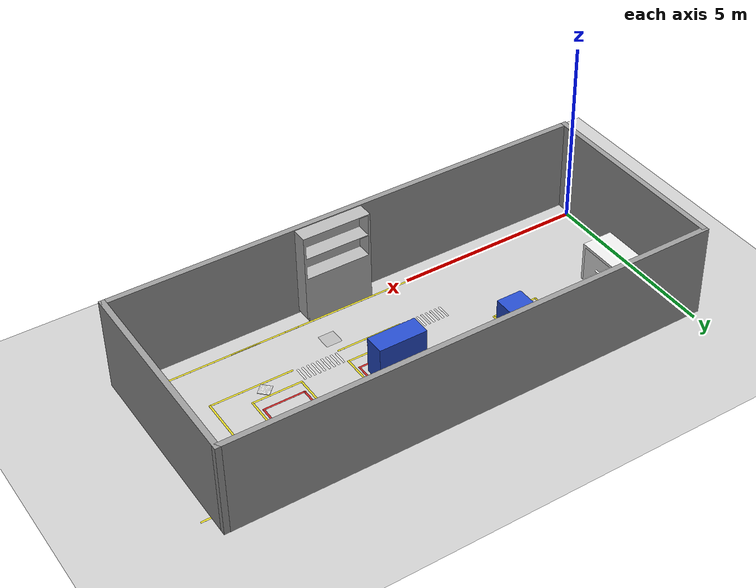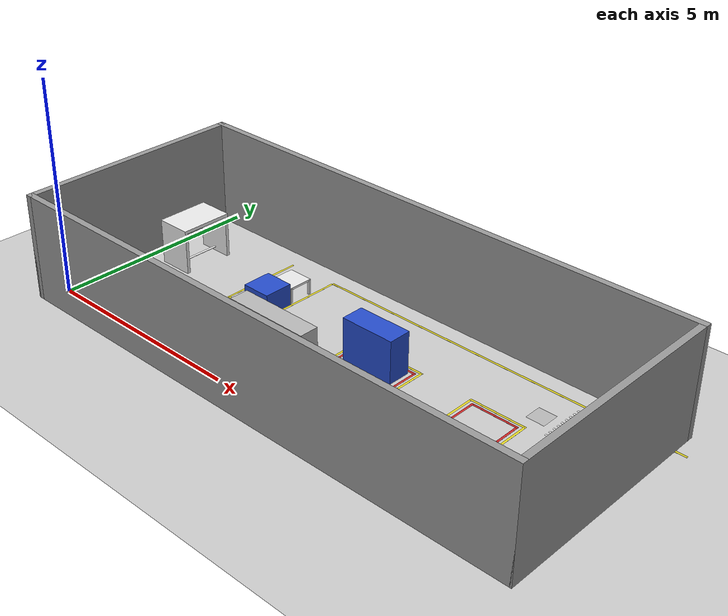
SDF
<sdf version="1.6">
 <world name="default">
  <light name="sun" type="directional">
   <pose>0 0 10 0 -0 0</pose>
   <diffuse>0.8 0.8 0.8 1</diffuse>
   <specular>0.2 0.2 0.2 1</specular>
   <attenuation>
    <range>1000</range>
    <constant>0.9</constant>
    <linear>0.01</linear>
    <quadratic>0.001</quadratic>
   </attenuation>
   <direction>-0.5 0.1 -0.9</direction>
  </light>
  <model name="ground_plane">
   <static>1</static>
   <link name="link">
    <collision name="collision">
     <geometry><plane><normal>0 0 1</normal><size>100 100</size></plane></geometry>
     <surface><friction><ode><mu>100</mu><mu2>50</mu2></ode></friction></surface>
    </collision>
    <visual name="visual">
     <cast_shadows>0</cast_shadows>
     <geometry><plane><normal>0 0 1</normal><size>100 100</size></plane></geometry>
     <material>
      <script><uri>file://media/materials/scripts/gazebo.material</uri><name>Gazebo/Grey</name></script>
     </material>
    </visual>
   </link>
  </model>
  <gravity>0 0 -9.8</gravity>
  <magnetic_field>6e-06 2.3e-05 -4.2e-05</magnetic_field>
  <atmosphere type="adiabatic"/>
  <physics name="default_physics" default="0" type="ode">
   <max_step_size>0.001</max_step_size>
   <real_time_factor>1</real_time_factor>
   <real_time_update_rate>1000</real_time_update_rate>
  </physics>
  <scene><ambient>0.4 0.4 0.4 1</ambient><background>0.7 0.7 0.7 1</background><shadows>1</shadows></scene>
  <spherical_coordinates>
   <surface_model>EARTH_WGS84</surface_model>
   <latitude_deg>0</latitude_deg>
   <longitude_deg>0</longitude_deg>
   <elevation>0</elevation>
   <heading_deg>0</heading_deg>
  </spherical_coordinates>
  <model name="newPedestrianSign">
   <link name="link_7">
    <inertial>
     <mass>1</mass>
     <inertia>
      <ixx>0.166667</ixx>
      <ixy>0</ixy>
      <ixz>0</ixz>
      <iyy>0.166667</iyy>
      <iyz>0</iyz>
      <izz>0.166667</izz>
     </inertia>
    </inertial>
    <visual name="visual">
     <pose>-0.2 -0.2 0 -1.5708 -0 0</pose>
     <geometry>
      <mesh><uri>model://newPedestrianSign/model/model.dae</uri><scale>0.5 0.5 0.5</scale></mesh>
     </geometry>
     <material><lighting>1</lighting></material>
    </visual>
    <collision name="collision">
     <pose>0 0 0 0 -0 0.785398</pose>
     <geometry><box><size>0.28 0.28 1e-05</size></box></geometry>
     <surface>
      <friction>
       <ode><mu>1</mu><mu2>1</mu2><fdir1>0 0 0</fdir1><slip1>0</slip1><slip2>0</slip2></ode>
       <torsional>
        <coefficient>1</coefficient>
        <patch_radius>0</patch_radius>
        <surface_radius>0</surface_radius>
        <use_patch_radius>1</use_patch_radius>
        <ode><slip>0</slip></ode>
       </torsional>
      </friction>
      <bounce><restitution_coefficient>0</restitution_coefficient><threshold>1e+06</threshold></bounce>
      <contact>
       <collide_without_contact>0</collide_without_contact>
       <collide_without_contact_bitmask>1</collide_without_contact_bitmask>
       <collide_bitmask>1</collide_bitmask>
       <ode>
        <soft_cfm>0</soft_cfm>
        <soft_erp>0.2</soft_erp>
        <kp>1e+13</kp>
        <kd>1</kd>
        <max_vel>0.01</max_vel>
        <min_depth>0</min_depth>
       </ode>
       <bullet>
        <split_impulse>1</split_impulse>
        <split_impulse_penetration_threshold>-0.01</split_impulse_penetration_threshold>
        <soft_cfm>0</soft_cfm>
        <soft_erp>0.2</soft_erp>
        <kp>1e+13</kp>
        <kd>1</kd>
       </bullet>
      </contact>
     </surface>
    </collision>
   </link>
   <static>1</static>
   <pose>6.96801 1.5365 0 0 -0 0</pose>
  </model>
  <model name="newPedestrianSign_0">
   <link name="link_7">
    <inertial>
     <mass>1</mass>
     <inertia>
      <ixx>0.166667</ixx>
      <ixy>0</ixy>
      <ixz>0</ixz>
      <iyy>0.166667</iyy>
      <iyz>0</iyz>
      <izz>0.166667</izz>
     </inertia>
    </inertial>
    <visual name="visual">
     <pose>-0.2 -0.2 0 -1.5708 -0 0</pose>
     <geometry>
      <mesh><uri>model://newPedestrianSign/model/model.dae</uri><scale>0.5 0.5 0.5</scale></mesh>
     </geometry>
     <material><lighting>1</lighting></material>
    </visual>
    <collision name="collision">
     <pose>0 0 0 0 -0 0.785398</pose>
     <geometry><box><size>0.28 0.28 1e-05</size></box></geometry>
     <surface>
      <friction>
       <ode><mu>1</mu><mu2>1</mu2><fdir1>0 0 0</fdir1><slip1>0</slip1><slip2>0</slip2></ode>
       <torsional>
        <coefficient>1</coefficient>
        <patch_radius>0</patch_radius>
        <surface_radius>0</surface_radius>
        <use_patch_radius>1</use_patch_radius>
        <ode><slip>0</slip></ode>
       </torsional>
      </friction>
      <bounce><restitution_coefficient>0</restitution_coefficient><threshold>1e+06</threshold></bounce>
      <contact>
       <collide_without_contact>0</collide_without_contact>
       <collide_without_contact_bitmask>1</collide_without_contact_bitmask>
       <collide_bitmask>1</collide_bitmask>
       <ode>
        <soft_cfm>0</soft_cfm>
        <soft_erp>0.2</soft_erp>
        <kp>1e+13</kp>
        <kd>1</kd>
        <max_vel>0.01</max_vel>
        <min_depth>0</min_depth>
       </ode>
       <bullet>
        <split_impulse>1</split_impulse>
        <split_impulse_penetration_threshold>-0.01</split_impulse_penetration_threshold>
        <soft_cfm>0</soft_cfm>
        <soft_erp>0.2</soft_erp>
        <kp>1e+13</kp>
        <kd>1</kd>
       </bullet>
      </contact>
     </surface>
    </collision>
   </link>
   <static>1</static>
   <pose>9.94353 1.54159 0 0 -0 0</pose>
  </model>
  <model name="line4m">
   <link name="link_3">
    <inertial>
     <mass>1</mass>
     <inertia>
      <ixx>0.166667</ixx>
      <ixy>0</ixy>
      <ixz>0</ixz>
      <iyy>0.166667</iyy>
      <iyz>0</iyz>
      <izz>0.166667</izz>
     </inertia>
    </inertial>
    <visual name="visual">
     <geometry><box><size>0.05 4 0.001</size></box></geometry>
     <material>
      <lighting>1</lighting>
      <script><uri>file://media/materials/scripts/gazebo.material</uri><name>Gazebo/Yellow</name></script>
     </material>
    </visual>
   </link>
   <static>1</static>
   <pose>6.8 0 0 0 -0 1.5708</pose>
  </model>
  <model name="line2m_0">
   <link name="link_0">
    <inertial>
     <mass>1</mass>
     <inertia>
      <ixx>0.166667</ixx>
      <ixy>0</ixy>
      <ixz>0</ixz>
      <iyy>0.166667</iyy>
      <iyz>0</iyz>
      <izz>0.166667</izz>
     </inertia>
    </inertial>
    <visual name="visual">
     <geometry><box><size>2 0.05 0.001</size></box></geometry>
     <material>
      <lighting>1</lighting>
      <script><uri>file://media/materials/scripts/gazebo.material</uri><name>Gazebo/Yellow</name></script>
     </material>
    </visual>
    <collision name="collision">
     <geometry><box><size>2 0.05 1e-05</size></box></geometry>
     <surface>
      <friction>
       <ode><mu>1</mu><mu2>1</mu2><fdir1>0 0 0</fdir1><slip1>0</slip1><slip2>0</slip2></ode>
       <torsional>
        <coefficient>1</coefficient>
        <patch_radius>0</patch_radius>
        <surface_radius>0</surface_radius>
        <use_patch_radius>1</use_patch_radius>
        <ode><slip>0</slip></ode>
       </torsional>
      </friction>
      <bounce><restitution_coefficient>0</restitution_coefficient><threshold>1e+06</threshold></bounce>
      <contact>
       <collide_without_contact>0</collide_without_contact>
       <collide_without_contact_bitmask>1</collide_without_contact_bitmask>
       <collide_bitmask>1</collide_bitmask>
       <ode>
        <soft_cfm>0</soft_cfm>
        <soft_erp>0.2</soft_erp>
        <kp>1e+13</kp>
        <kd>1</kd>
        <max_vel>0.01</max_vel>
        <min_depth>0</min_depth>
       </ode>
       <bullet>
        <split_impulse>1</split_impulse>
        <split_impulse_penetration_threshold>-0.01</split_impulse_penetration_threshold>
        <soft_cfm>0</soft_cfm>
        <soft_erp>0.2</soft_erp>
        <kp>1e+13</kp>
        <kd>1</kd>
       </bullet>
      </contact>
     </surface>
    </collision>
   </link>
   <static>1</static>
   <pose>9.13049 0 0 0 -0 0</pose>
  </model>
  <model name="line9m">
   <link name="link_1">
    <inertial>
     <mass>1</mass>
     <inertia>
      <ixx>0.166667</ixx>
      <ixy>0</ixy>
      <ixz>0</ixz>
      <iyy>0.166667</iyy>
      <iyz>0</iyz>
      <izz>0.166667</izz>
     </inertia>
    </inertial>
    <visual name="visual">
     <geometry><box><size>9 0.05 0.001</size></box></geometry>
     <material>
      <lighting>1</lighting>
      <script><uri>file://media/materials/scripts/gazebo.material</uri><name>Gazebo/Yellow</name></script>
     </material>
    </visual>
   </link>
   <static>1</static>
   <pose>8.5 4.3 0 0 -0 0</pose>
  </model>
  <model name="line2m_1">
   <link name="link_0">
    <inertial>
     <mass>1</mass>
     <inertia>
      <ixx>0.166667</ixx>
      <ixy>0</ixy>
      <ixz>0</ixz>
      <iyy>0.166667</iyy>
      <iyz>0</iyz>
      <izz>0.166667</izz>
     </inertia>
    </inertial>
    <visual name="visual">
     <geometry><box><size>2 0.05 0.001</size></box></geometry>
     <material>
      <lighting>1</lighting>
      <script><uri>file://media/materials/scripts/gazebo.material</uri><name>Gazebo/Yellow</name></script>
     </material>
    </visual>
    <collision name="collision">
     <geometry><box><size>2 0.05 1e-05</size></box></geometry>
     <surface>
      <friction>
       <ode><mu>1</mu><mu2>1</mu2><fdir1>0 0 0</fdir1><slip1>0</slip1><slip2>0</slip2></ode>
       <torsional>
        <coefficient>1</coefficient>
        <patch_radius>0</patch_radius>
        <surface_radius>0</surface_radius>
        <use_patch_radius>1</use_patch_radius>
        <ode><slip>0</slip></ode>
       </torsional>
      </friction>
      <bounce><restitution_coefficient>0</restitution_coefficient><threshold>1e+06</threshold></bounce>
      <contact>
       <collide_without_contact>0</collide_without_contact>
       <collide_without_contact_bitmask>1</collide_without_contact_bitmask>
       <collide_bitmask>1</collide_bitmask>
       <ode>
        <soft_cfm>0</soft_cfm>
        <soft_erp>0.2</soft_erp>
        <kp>1e+13</kp>
        <kd>1</kd>
        <max_vel>0.01</max_vel>
        <min_depth>0</min_depth>
       </ode>
       <bullet>
        <split_impulse>1</split_impulse>
        <split_impulse_penetration_threshold>-0.01</split_impulse_penetration_threshold>
        <soft_cfm>0</soft_cfm>
        <soft_erp>0.2</soft_erp>
        <kp>1e+13</kp>
        <kd>1</kd>
       </bullet>
      </contact>
     </surface>
    </collision>
   </link>
   <static>1</static>
   <pose>12.47 1.00117 0 0 -0 1.5708</pose>
  </model>
  <model name="forkliftRoadSign">
   <link name="link_7">
    <inertial>
     <mass>1</mass>
     <inertia>
      <ixx>0.166667</ixx>
      <ixy>0</ixy>
      <ixz>0</ixz>
      <iyy>0.166667</iyy>
      <iyz>0</iyz>
      <izz>0.166667</izz>
     </inertia>
    </inertial>
    <visual name="visual">
     <pose>-0.2 -0.2 0.01 -1.5708 -0 0</pose>
     <geometry>
      <mesh><uri>model://forkliftRoadSign/model/model.dae</uri><scale>0.7 0.7 0.7</scale></mesh>
     </geometry>
     <material><lighting>1</lighting></material>
    </visual>
   </link>
   <static>1</static>
   <pose>7.75 0.8 0 0 -0 1.5708</pose>
  </model>
  <model name="forkliftRoadSign_0">
   <link name="link_7">
    <inertial>
     <mass>1</mass>
     <inertia>
      <ixx>0.166667</ixx>
      <ixy>0</ixy>
      <ixz>0</ixz>
      <iyy>0.166667</iyy>
      <iyz>0</iyz>
      <izz>0.166667</izz>
     </inertia>
    </inertial>
    <visual name="visual">
     <pose>-0.2 -0.2 0.01 -1.5708 -0 0</pose>
     <geometry>
      <mesh><uri>model://forkliftRoadSign/model/model.dae</uri><scale>0.7 0.7 0.7</scale></mesh>
     </geometry>
     <material><lighting>1</lighting></material>
    </visual>
   </link>
   <static>1</static>
   <pose>10.3501 3.4718 0 0 0 -1.5708</pose>
  </model>
  <model name="forkliftRoadSign_1">
   <link name="link_7">
    <inertial>
     <mass>1</mass>
     <inertia>
      <ixx>0.166667</ixx>
      <ixy>0</ixy>
      <ixz>0</ixz>
      <iyy>0.166667</iyy>
      <iyz>0</iyz>
      <izz>0.166667</izz>
     </inertia>
    </inertial>
    <visual name="visual">
     <pose>-0.2 -0.2 0.01 -1.5708 -0 0</pose>
     <geometry>
      <mesh><uri>model://forkliftRoadSign/model/model.dae</uri><scale>0.7 0.7 0.7</scale></mesh>
     </geometry>
     <material><lighting>1</lighting></material>
    </visual>
   </link>
   <static>1</static>
   <pose>6.37777 3.72064 0 0 0 -1.5708</pose>
  </model>
  <model name="cocktail_table">
   <link name="link_1">
    <inertial>
     <mass>1</mass>
     <inertia>
      <ixx>0.166667</ixx>
      <ixy>0</ixy>
      <ixz>0</ixz>
      <iyy>0.166667</iyy>
      <iyz>0</iyz>
      <izz>0.166667</izz>
     </inertia>
    </inertial>
    <visual name="visual">
     <pose>0.42 -0.71 -0.505 0 -0 1.5708</pose>
     <geometry>
      <mesh><uri>model://cocktail_table/model/model.dae</uri><scale>0.96 1.4 0.95</scale></mesh>
     </geometry>
     <material>
      <lighting>1</lighting>
      <script><uri>file://media/materials/scripts/gazebo.material</uri><name>Gazebo/White</name></script>
     </material>
    </visual>
    <collision name="collision">
     <geometry><box><size>0.84 1.26 1.05</size></box></geometry>
     <surface>
      <friction>
       <ode><mu>1</mu><mu2>1</mu2><fdir1>0 0 0</fdir1><slip1>0</slip1><slip2>0</slip2></ode>
       <torsional>
        <coefficient>1</coefficient>
        <patch_radius>0</patch_radius>
        <surface_radius>0</surface_radius>
        <use_patch_radius>1</use_patch_radius>
        <ode><slip>0</slip></ode>
       </torsional>
      </friction>
      <bounce><restitution_coefficient>0</restitution_coefficient><threshold>1e+06</threshold></bounce>
      <contact>
       <collide_without_contact>0</collide_without_contact>
       <collide_without_contact_bitmask>1</collide_without_contact_bitmask>
       <collide_bitmask>1</collide_bitmask>
       <ode>
        <soft_cfm>0</soft_cfm>
        <soft_erp>0.2</soft_erp>
        <kp>1e+13</kp>
        <kd>1</kd>
        <max_vel>0.01</max_vel>
        <min_depth>0</min_depth>
       </ode>
       <bullet>
        <split_impulse>1</split_impulse>
        <split_impulse_penetration_threshold>-0.01</split_impulse_penetration_threshold>
        <soft_cfm>0</soft_cfm>
        <soft_erp>0.2</soft_erp>
        <kp>1e+13</kp>
        <kd>1</kd>
       </bullet>
      </contact>
     </surface>
    </collision>
   </link>
   <static>1</static>
   <pose>0.917342 2.93643 0.525321 0 -0 0</pose>
  </model>
  <model name="zebraCrossing9">
   <link name="link_0">
    <inertial>
     <mass>1</mass>
     <inertia>
      <ixx>0.166667</ixx>
      <ixy>0</ixy>
      <ixz>0</ixz>
      <iyy>0.166667</iyy>
      <iyz>0</iyz>
      <izz>0.166667</izz>
     </inertia>
    </inertial>
    <visual name="visual">
     <geometry><box><size>0.05 0.4 0.001</size></box></geometry>
     <material>
      <lighting>1</lighting>
      <script><uri>file://media/materials/scripts/gazebo.material</uri><name>Gazebo/White</name></script>
      <shader type="pixel"><normal_map>__default__</normal_map></shader>
      <ambient>1 1 1 1</ambient>
      <diffuse>1 1 1 1</diffuse>
      <specular>0.01 0.01 0.01 1</specular>
      <emissive>0 0 0 1</emissive>
     </material>
     <cast_shadows>0</cast_shadows>
    </visual>
    <visual name="ModelPreview_0::link_0::visual_1">
     <pose>0.13 0 0 0 -0 0</pose>
     <geometry><box><size>0.05 0.4 0.001</size></box></geometry>
     <material>
      <lighting>1</lighting>
      <script><uri>file://media/materials/scripts/gazebo.material</uri><name>Gazebo/White</name></script>
      <shader type="pixel"><normal_map>__default__</normal_map></shader>
      <ambient>1 1 1 1</ambient>
      <diffuse>1 1 1 1</diffuse>
      <specular>0.01 0.01 0.01 1</specular>
      <emissive>0 0 0 1</emissive>
     </material>
     <cast_shadows>0</cast_shadows>
    </visual>
    <visual name="ModelPreview_0::link_0::visual_2">
     <pose>0.26 0 0 0 -0 0</pose>
     <geometry><box><size>0.05 0.4 0.001</size></box></geometry>
     <material>
      <lighting>1</lighting>
      <script><uri>file://media/materials/scripts/gazebo.material</uri><name>Gazebo/White</name></script>
      <shader type="pixel"><normal_map>__default__</normal_map></shader>
      <ambient>1 1 1 1</ambient>
      <diffuse>1 1 1 1</diffuse>
      <specular>0.01 0.01 0.01 1</specular>
      <emissive>0 0 0 1</emissive>
     </material>
     <cast_shadows>0</cast_shadows>
    </visual>
    <visual name="ModelPreview_0::link_0::visual_3">
     <pose>0.39 0 0 0 -0 0</pose>
     <geometry><box><size>0.05 0.4 0.001</size></box></geometry>
     <material>
      <lighting>1</lighting>
      <script><uri>file://media/materials/scripts/gazebo.material</uri><name>Gazebo/White</name></script>
      <shader type="pixel"><normal_map>__default__</normal_map></shader>
      <ambient>1 1 1 1</ambient>
      <diffuse>1 1 1 1</diffuse>
      <specular>0.01 0.01 0.01 1</specular>
      <emissive>0 0 0 1</emissive>
     </material>
     <cast_shadows>0</cast_shadows>
    </visual>
    <visual name="ModelPreview_0::link_0::visual_4">
     <pose>0.52 0 0 0 -0 0</pose>
     <geometry><box><size>0.05 0.4 0.001</size></box></geometry>
     <material>
      <lighting>1</lighting>
      <script><uri>file://media/materials/scripts/gazebo.material</uri><name>Gazebo/White</name></script>
      <shader type="pixel"><normal_map>__default__</normal_map></shader>
      <ambient>1 1 1 1</ambient>
      <diffuse>1 1 1 1</diffuse>
      <specular>0.01 0.01 0.01 1</specular>
      <emissive>0 0 0 1</emissive>
     </material>
     <cast_shadows>0</cast_shadows>
    </visual>
    <visual name="ModelPreview_0::link_0::visual_5">
     <pose>-0.13 0 0 0 -0 0</pose>
     <geometry><box><size>0.05 0.4 0.001</size></box></geometry>
     <material>
      <lighting>1</lighting>
      <script><uri>file://media/materials/scripts/gazebo.material</uri><name>Gazebo/White</name></script>
      <shader type="pixel"><normal_map>__default__</normal_map></shader>
      <ambient>1 1 1 1</ambient>
      <diffuse>1 1 1 1</diffuse>
      <specular>0.01 0.01 0.01 1</specular>
      <emissive>0 0 0 1</emissive>
     </material>
     <cast_shadows>0</cast_shadows>
    </visual>
    <visual name="ModelPreview_0::link_0::visual_6">
     <pose>-0.26 0 0 0 -0 0</pose>
     <geometry><box><size>0.05 0.4 0.001</size></box></geometry>
     <material>
      <lighting>1</lighting>
      <script><uri>file://media/materials/scripts/gazebo.material</uri><name>Gazebo/White</name></script>
      <shader type="pixel"><normal_map>__default__</normal_map></shader>
      <ambient>1 1 1 1</ambient>
      <diffuse>1 1 1 1</diffuse>
      <specular>0.01 0.01 0.01 1</specular>
      <emissive>0 0 0 1</emissive>
     </material>
     <cast_shadows>0</cast_shadows>
    </visual>
    <visual name="ModelPreview_0::link_0::visual_7">
     <pose>-0.39 0 0 0 -0 0</pose>
     <geometry><box><size>0.05 0.4 0.001</size></box></geometry>
     <material>
      <lighting>1</lighting>
      <script><uri>file://media/materials/scripts/gazebo.material</uri><name>Gazebo/White</name></script>
      <shader type="pixel"><normal_map>__default__</normal_map></shader>
      <ambient>1 1 1 1</ambient>
      <diffuse>1 1 1 1</diffuse>
      <specular>0.01 0.01 0.01 1</specular>
      <emissive>0 0 0 1</emissive>
     </material>
     <cast_shadows>0</cast_shadows>
    </visual>
    <visual name="ModelPreview_0::link_0::visual_8">
     <pose>-0.52 0 0 0 -0 0</pose>
     <geometry><box><size>0.05 0.4 0.001</size></box></geometry>
     <material>
      <lighting>1</lighting>
      <script><uri>file://media/materials/scripts/gazebo.material</uri><name>Gazebo/White</name></script>
      <shader type="pixel"><normal_map>__default__</normal_map></shader>
      <ambient>1 1 1 1</ambient>
      <diffuse>1 1 1 1</diffuse>
      <specular>0.01 0.01 0.01 1</specular>
      <emissive>0 0 0 1</emissive>
     </material>
     <cast_shadows>0</cast_shadows>
    </visual>
   </link>
   <static>1</static>
   <pose>5.43019 1.45864 0 0 -0 0</pose>
  </model>
  <model name="zebraCrossing9_0">
   <link name="link_0">
    <inertial>
     <mass>1</mass>
     <inertia>
      <ixx>0.166667</ixx>
      <ixy>0</ixy>
      <ixz>0</ixz>
      <iyy>0.166667</iyy>
      <iyz>0</iyz>
      <izz>0.166667</izz>
     </inertia>
    </inertial>
    <visual name="visual">
     <geometry><box><size>0.05 0.4 0.001</size></box></geometry>
     <material>
      <lighting>1</lighting>
      <script><uri>file://media/materials/scripts/gazebo.material</uri><name>Gazebo/White</name></script>
      <shader type="pixel"><normal_map>__default__</normal_map></shader>
      <ambient>1 1 1 1</ambient>
      <diffuse>1 1 1 1</diffuse>
      <specular>0.01 0.01 0.01 1</specular>
      <emissive>0 0 0 1</emissive>
     </material>
     <cast_shadows>0</cast_shadows>
    </visual>
    <visual name="ModelPreview_0::link_0::visual_1">
     <pose>0.13 0 0 0 -0 0</pose>
     <geometry><box><size>0.05 0.4 0.001</size></box></geometry>
     <material>
      <lighting>1</lighting>
      <script><uri>file://media/materials/scripts/gazebo.material</uri><name>Gazebo/White</name></script>
      <shader type="pixel"><normal_map>__default__</normal_map></shader>
      <ambient>1 1 1 1</ambient>
      <diffuse>1 1 1 1</diffuse>
      <specular>0.01 0.01 0.01 1</specular>
      <emissive>0 0 0 1</emissive>
     </material>
     <cast_shadows>0</cast_shadows>
    </visual>
    <visual name="ModelPreview_0::link_0::visual_2">
     <pose>0.26 0 0 0 -0 0</pose>
     <geometry><box><size>0.05 0.4 0.001</size></box></geometry>
     <material>
      <lighting>1</lighting>
      <script><uri>file://media/materials/scripts/gazebo.material</uri><name>Gazebo/White</name></script>
      <shader type="pixel"><normal_map>__default__</normal_map></shader>
      <ambient>1 1 1 1</ambient>
      <diffuse>1 1 1 1</diffuse>
      <specular>0.01 0.01 0.01 1</specular>
      <emissive>0 0 0 1</emissive>
     </material>
     <cast_shadows>0</cast_shadows>
    </visual>
    <visual name="ModelPreview_0::link_0::visual_3">
     <pose>0.39 0 0 0 -0 0</pose>
     <geometry><box><size>0.05 0.4 0.001</size></box></geometry>
     <material>
      <lighting>1</lighting>
      <script><uri>file://media/materials/scripts/gazebo.material</uri><name>Gazebo/White</name></script>
      <shader type="pixel"><normal_map>__default__</normal_map></shader>
      <ambient>1 1 1 1</ambient>
      <diffuse>1 1 1 1</diffuse>
      <specular>0.01 0.01 0.01 1</specular>
      <emissive>0 0 0 1</emissive>
     </material>
     <cast_shadows>0</cast_shadows>
    </visual>
    <visual name="ModelPreview_0::link_0::visual_4">
     <pose>0.52 0 0 0 -0 0</pose>
     <geometry><box><size>0.05 0.4 0.001</size></box></geometry>
     <material>
      <lighting>1</lighting>
      <script><uri>file://media/materials/scripts/gazebo.material</uri><name>Gazebo/White</name></script>
      <shader type="pixel"><normal_map>__default__</normal_map></shader>
      <ambient>1 1 1 1</ambient>
      <diffuse>1 1 1 1</diffuse>
      <specular>0.01 0.01 0.01 1</specular>
      <emissive>0 0 0 1</emissive>
     </material>
     <cast_shadows>0</cast_shadows>
    </visual>
    <visual name="ModelPreview_0::link_0::visual_5">
     <pose>-0.13 0 0 0 -0 0</pose>
     <geometry><box><size>0.05 0.4 0.001</size></box></geometry>
     <material>
      <lighting>1</lighting>
      <script><uri>file://media/materials/scripts/gazebo.material</uri><name>Gazebo/White</name></script>
      <shader type="pixel"><normal_map>__default__</normal_map></shader>
      <ambient>1 1 1 1</ambient>
      <diffuse>1 1 1 1</diffuse>
      <specular>0.01 0.01 0.01 1</specular>
      <emissive>0 0 0 1</emissive>
     </material>
     <cast_shadows>0</cast_shadows>
    </visual>
    <visual name="ModelPreview_0::link_0::visual_6">
     <pose>-0.26 0 0 0 -0 0</pose>
     <geometry><box><size>0.05 0.4 0.001</size></box></geometry>
     <material>
      <lighting>1</lighting>
      <script><uri>file://media/materials/scripts/gazebo.material</uri><name>Gazebo/White</name></script>
      <shader type="pixel"><normal_map>__default__</normal_map></shader>
      <ambient>1 1 1 1</ambient>
      <diffuse>1 1 1 1</diffuse>
      <specular>0.01 0.01 0.01 1</specular>
      <emissive>0 0 0 1</emissive>
     </material>
     <cast_shadows>0</cast_shadows>
    </visual>
    <visual name="ModelPreview_0::link_0::visual_7">
     <pose>-0.39 0 0 0 -0 0</pose>
     <geometry><box><size>0.05 0.4 0.001</size></box></geometry>
     <material>
      <lighting>1</lighting>
      <script><uri>file://media/materials/scripts/gazebo.material</uri><name>Gazebo/White</name></script>
      <shader type="pixel"><normal_map>__default__</normal_map></shader>
      <ambient>1 1 1 1</ambient>
      <diffuse>1 1 1 1</diffuse>
      <specular>0.01 0.01 0.01 1</specular>
      <emissive>0 0 0 1</emissive>
     </material>
     <cast_shadows>0</cast_shadows>
    </visual>
    <visual name="ModelPreview_0::link_0::visual_8">
     <pose>-0.52 0 0 0 -0 0</pose>
     <geometry><box><size>0.05 0.4 0.001</size></box></geometry>
     <material>
      <lighting>1</lighting>
      <script><uri>file://media/materials/scripts/gazebo.material</uri><name>Gazebo/White</name></script>
      <shader type="pixel"><normal_map>__default__</normal_map></shader>
      <ambient>1 1 1 1</ambient>
      <diffuse>1 1 1 1</diffuse>
      <specular>0.01 0.01 0.01 1</specular>
      <emissive>0 0 0 1</emissive>
     </material>
     <cast_shadows>0</cast_shadows>
    </visual>
   </link>
   <static>1</static>
   <pose>8.4 1.5 0 0 -0 0</pose>
  </model>
  <model name="zebraCrossing9_1">
   <link name="link_0">
    <inertial>
     <mass>1</mass>
     <inertia>
      <ixx>0.166667</ixx>
      <ixy>0</ixy>
      <ixz>0</ixz>
      <iyy>0.166667</iyy>
      <iyz>0</iyz>
      <izz>0.166667</izz>
     </inertia>
    </inertial>
    <visual name="visual">
     <geometry><box><size>0.05 0.4 0.001</size></box></geometry>
     <material>
      <lighting>1</lighting>
      <script><uri>file://media/materials/scripts/gazebo.material</uri><name>Gazebo/White</name></script>
      <shader type="pixel"><normal_map>__default__</normal_map></shader>
      <ambient>1 1 1 1</ambient>
      <diffuse>1 1 1 1</diffuse>
      <specular>0.01 0.01 0.01 1</specular>
      <emissive>0 0 0 1</emissive>
     </material>
     <cast_shadows>0</cast_shadows>
    </visual>
    <visual name="ModelPreview_0::link_0::visual_1">
     <pose>0.13 0 0 0 -0 0</pose>
     <geometry><box><size>0.05 0.4 0.001</size></box></geometry>
     <material>
      <lighting>1</lighting>
      <script><uri>file://media/materials/scripts/gazebo.material</uri><name>Gazebo/White</name></script>
      <shader type="pixel"><normal_map>__default__</normal_map></shader>
      <ambient>1 1 1 1</ambient>
      <diffuse>1 1 1 1</diffuse>
      <specular>0.01 0.01 0.01 1</specular>
      <emissive>0 0 0 1</emissive>
     </material>
     <cast_shadows>0</cast_shadows>
    </visual>
    <visual name="ModelPreview_0::link_0::visual_2">
     <pose>0.26 0 0 0 -0 0</pose>
     <geometry><box><size>0.05 0.4 0.001</size></box></geometry>
     <material>
      <lighting>1</lighting>
      <script><uri>file://media/materials/scripts/gazebo.material</uri><name>Gazebo/White</name></script>
      <shader type="pixel"><normal_map>__default__</normal_map></shader>
      <ambient>1 1 1 1</ambient>
      <diffuse>1 1 1 1</diffuse>
      <specular>0.01 0.01 0.01 1</specular>
      <emissive>0 0 0 1</emissive>
     </material>
     <cast_shadows>0</cast_shadows>
    </visual>
    <visual name="ModelPreview_0::link_0::visual_3">
     <pose>0.39 0 0 0 -0 0</pose>
     <geometry><box><size>0.05 0.4 0.001</size></box></geometry>
     <material>
      <lighting>1</lighting>
      <script><uri>file://media/materials/scripts/gazebo.material</uri><name>Gazebo/White</name></script>
      <shader type="pixel"><normal_map>__default__</normal_map></shader>
      <ambient>1 1 1 1</ambient>
      <diffuse>1 1 1 1</diffuse>
      <specular>0.01 0.01 0.01 1</specular>
      <emissive>0 0 0 1</emissive>
     </material>
     <cast_shadows>0</cast_shadows>
    </visual>
    <visual name="ModelPreview_0::link_0::visual_4">
     <pose>0.52 0 0 0 -0 0</pose>
     <geometry><box><size>0.05 0.4 0.001</size></box></geometry>
     <material>
      <lighting>1</lighting>
      <script><uri>file://media/materials/scripts/gazebo.material</uri><name>Gazebo/White</name></script>
      <shader type="pixel"><normal_map>__default__</normal_map></shader>
      <ambient>1 1 1 1</ambient>
      <diffuse>1 1 1 1</diffuse>
      <specular>0.01 0.01 0.01 1</specular>
      <emissive>0 0 0 1</emissive>
     </material>
     <cast_shadows>0</cast_shadows>
    </visual>
    <visual name="ModelPreview_0::link_0::visual_5">
     <pose>-0.13 0 0 0 -0 0</pose>
     <geometry><box><size>0.05 0.4 0.001</size></box></geometry>
     <material>
      <lighting>1</lighting>
      <script><uri>file://media/materials/scripts/gazebo.material</uri><name>Gazebo/White</name></script>
      <shader type="pixel"><normal_map>__default__</normal_map></shader>
      <ambient>1 1 1 1</ambient>
      <diffuse>1 1 1 1</diffuse>
      <specular>0.01 0.01 0.01 1</specular>
      <emissive>0 0 0 1</emissive>
     </material>
     <cast_shadows>0</cast_shadows>
    </visual>
    <visual name="ModelPreview_0::link_0::visual_6">
     <pose>-0.26 0 0 0 -0 0</pose>
     <geometry><box><size>0.05 0.4 0.001</size></box></geometry>
     <material>
      <lighting>1</lighting>
      <script><uri>file://media/materials/scripts/gazebo.material</uri><name>Gazebo/White</name></script>
      <shader type="pixel"><normal_map>__default__</normal_map></shader>
      <ambient>1 1 1 1</ambient>
      <diffuse>1 1 1 1</diffuse>
      <specular>0.01 0.01 0.01 1</specular>
      <emissive>0 0 0 1</emissive>
     </material>
     <cast_shadows>0</cast_shadows>
    </visual>
    <visual name="ModelPreview_0::link_0::visual_7">
     <pose>-0.39 0 0 0 -0 0</pose>
     <geometry><box><size>0.05 0.4 0.001</size></box></geometry>
     <material>
      <lighting>1</lighting>
      <script><uri>file://media/materials/scripts/gazebo.material</uri><name>Gazebo/White</name></script>
      <shader type="pixel"><normal_map>__default__</normal_map></shader>
      <ambient>1 1 1 1</ambient>
      <diffuse>1 1 1 1</diffuse>
      <specular>0.01 0.01 0.01 1</specular>
      <emissive>0 0 0 1</emissive>
     </material>
     <cast_shadows>0</cast_shadows>
    </visual>
    <visual name="ModelPreview_0::link_0::visual_8">
     <pose>-0.52 0 0 0 -0 0</pose>
     <geometry><box><size>0.05 0.4 0.001</size></box></geometry>
     <material>
      <lighting>1</lighting>
      <script><uri>file://media/materials/scripts/gazebo.material</uri><name>Gazebo/White</name></script>
      <shader type="pixel"><normal_map>__default__</normal_map></shader>
      <ambient>1 1 1 1</ambient>
      <diffuse>1 1 1 1</diffuse>
      <specular>0.01 0.01 0.01 1</specular>
      <emissive>0 0 0 1</emissive>
     </material>
     <cast_shadows>0</cast_shadows>
    </visual>
   </link>
   <static>1</static>
   <pose>10.9351 3.58011 0 0 -0 1.5708</pose>
  </model>
  <model name="line175cm">
   <link name="link_1">
    <inertial>
     <mass>1</mass>
     <inertia>
      <ixx>0.166667</ixx>
      <ixy>0</ixy>
      <ixz>0</ixz>
      <iyy>0.166667</iyy>
      <iyz>0</iyz>
      <izz>0.166667</izz>
     </inertia>
    </inertial>
    <visual name="visual">
     <geometry><box><size>1.75 0.05 0.001</size></box></geometry>
     <material>
      <script><uri>file://media/materials/scripts/gazebo.material</uri><name>Gazebo/Yellow</name></script>
     </material>
    </visual>
    <collision name="collision">
     <geometry><box><size>1.75 0.05 1e-05</size></box></geometry>
     <surface>
      <friction>
       <ode><mu>1</mu><mu2>1</mu2><fdir1>0 0 0</fdir1><slip1>0</slip1><slip2>0</slip2></ode>
       <torsional>
        <coefficient>1</coefficient>
        <patch_radius>0</patch_radius>
        <surface_radius>0</surface_radius>
        <use_patch_radius>1</use_patch_radius>
        <ode><slip>0</slip></ode>
       </torsional>
      </friction>
      <bounce><restitution_coefficient>0</restitution_coefficient><threshold>1e+06</threshold></bounce>
      <contact>
       <collide_without_contact>0</collide_without_contact>
       <collide_without_contact_bitmask>1</collide_without_contact_bitmask>
       <collide_bitmask>1</collide_bitmask>
       <ode>
        <soft_cfm>0</soft_cfm>
        <soft_erp>0.2</soft_erp>
        <kp>1e+13</kp>
        <kd>1</kd>
        <max_vel>0.01</max_vel>
        <min_depth>0</min_depth>
       </ode>
       <bullet>
        <split_impulse>1</split_impulse>
        <split_impulse_penetration_threshold>-0.01</split_impulse_penetration_threshold>
        <soft_cfm>0</soft_cfm>
        <soft_erp>0.2</soft_erp>
        <kp>1e+13</kp>
        <kd>1</kd>
       </bullet>
      </contact>
     </surface>
    </collision>
   </link>
   <static>1</static>
   <pose>11.19 2.12334 0 0 -0 1.5708</pose>
  </model>
  <model name="line220cm">
   <link name="link_1">
    <inertial>
     <mass>1</mass>
     <inertia>
      <ixx>0.166667</ixx>
      <ixy>0</ixy>
      <ixz>0</ixz>
      <iyy>0.166667</iyy>
      <iyz>0</iyz>
      <izz>0.166667</izz>
     </inertia>
    </inertial>
    <visual name="visual">
     <geometry><box><size>2.2 0.05 0.001</size></box></geometry>
     <material>
      <script><uri>file://media/materials/scripts/gazebo.material</uri><name>Gazebo/Yellow</name></script>
     </material>
    </visual>
    <collision name="collision">
     <geometry><box><size>2.2 0.05 1e-05</size></box></geometry>
     <surface>
      <friction>
       <ode><mu>1</mu><mu2>1</mu2><fdir1>0 0 0</fdir1><slip1>0</slip1><slip2>0</slip2></ode>
       <torsional>
        <coefficient>1</coefficient>
        <patch_radius>0</patch_radius>
        <surface_radius>0</surface_radius>
        <use_patch_radius>1</use_patch_radius>
        <ode><slip>0</slip></ode>
       </torsional>
      </friction>
      <bounce><restitution_coefficient>0</restitution_coefficient><threshold>1e+06</threshold></bounce>
      <contact>
       <collide_without_contact>0</collide_without_contact>
       <collide_without_contact_bitmask>1</collide_without_contact_bitmask>
       <collide_bitmask>1</collide_bitmask>
       <ode>
        <soft_cfm>0</soft_cfm>
        <soft_erp>0.2</soft_erp>
        <kp>1e+13</kp>
        <kd>1</kd>
        <max_vel>0.01</max_vel>
        <min_depth>0</min_depth>
       </ode>
       <bullet>
        <split_impulse>1</split_impulse>
        <split_impulse_penetration_threshold>-0.01</split_impulse_penetration_threshold>
        <soft_cfm>0</soft_cfm>
        <soft_erp>0.2</soft_erp>
        <kp>1e+13</kp>
        <kd>1</kd>
       </bullet>
      </contact>
     </surface>
    </collision>
   </link>
   <static>1</static>
   <pose>10.115 1.27 0 0 -0 0</pose>
  </model>
  <model name="line134cm">
   <link name="link_1">
    <inertial>
     <mass>1</mass>
     <inertia>
      <ixx>0.166667</ixx>
      <ixy>0</ixy>
      <ixz>0</ixz>
      <iyy>0.166667</iyy>
      <iyz>0</iyz>
      <izz>0.166667</izz>
     </inertia>
    </inertial>
    <visual name="visual">
     <geometry><box><size>1.34 0.05 0.001</size></box></geometry>
     <material>
      <script><uri>file://media/materials/scripts/gazebo.material</uri><name>Gazebo/Yellow</name></script>
     </material>
    </visual>
    <collision name="collision">
     <geometry><box><size>1.34 0.05 1e-05</size></box></geometry>
     <surface>
      <friction>
       <ode><mu>1</mu><mu2>1</mu2><fdir1>0 0 0</fdir1><slip1>0</slip1><slip2>0</slip2></ode>
       <torsional>
        <coefficient>1</coefficient>
        <patch_radius>0</patch_radius>
        <surface_radius>0</surface_radius>
        <use_patch_radius>1</use_patch_radius>
        <ode><slip>0</slip></ode>
       </torsional>
      </friction>
      <bounce><restitution_coefficient>0</restitution_coefficient><threshold>1e+06</threshold></bounce>
      <contact>
       <collide_without_contact>0</collide_without_contact>
       <collide_without_contact_bitmask>1</collide_without_contact_bitmask>
       <collide_bitmask>1</collide_bitmask>
       <ode>
        <soft_cfm>0</soft_cfm>
        <soft_erp>0.2</soft_erp>
        <kp>1e+13</kp>
        <kd>1</kd>
        <max_vel>0.01</max_vel>
        <min_depth>0</min_depth>
       </ode>
       <bullet>
        <split_impulse>1</split_impulse>
        <split_impulse_penetration_threshold>-0.01</split_impulse_penetration_threshold>
        <soft_cfm>0</soft_cfm>
        <soft_erp>0.2</soft_erp>
        <kp>1e+13</kp>
        <kd>1</kd>
       </bullet>
      </contact>
     </surface>
    </collision>
   </link>
   <static>1</static>
   <pose>9.69 1.72 0 0 -0 0</pose>
  </model>
  <model name="line134cm_0">
   <link name="link_1">
    <inertial>
     <mass>1</mass>
     <inertia>
      <ixx>0.166667</ixx>
      <ixy>0</ixy>
      <ixz>0</ixz>
      <iyy>0.166667</iyy>
      <iyz>0</iyz>
      <izz>0.166667</izz>
     </inertia>
    </inertial>
    <visual name="visual">
     <geometry><box><size>1.34 0.05 0.001</size></box></geometry>
     <material>
      <script><uri>file://media/materials/scripts/gazebo.material</uri><name>Gazebo/Yellow</name></script>
     </material>
    </visual>
    <collision name="collision">
     <geometry><box><size>1.34 0.05 1e-05</size></box></geometry>
     <surface>
      <friction>
       <ode><mu>1</mu><mu2>1</mu2><fdir1>0 0 0</fdir1><slip1>0</slip1><slip2>0</slip2></ode>
       <torsional>
        <coefficient>1</coefficient>
        <patch_radius>0</patch_radius>
        <surface_radius>0</surface_radius>
        <use_patch_radius>1</use_patch_radius>
        <ode><slip>0</slip></ode>
       </torsional>
      </friction>
      <bounce><restitution_coefficient>0</restitution_coefficient><threshold>1e+06</threshold></bounce>
      <contact>
       <collide_without_contact>0</collide_without_contact>
       <collide_without_contact_bitmask>1</collide_without_contact_bitmask>
       <collide_bitmask>1</collide_bitmask>
       <ode>
        <soft_cfm>0</soft_cfm>
        <soft_erp>0.2</soft_erp>
        <kp>1e+13</kp>
        <kd>1</kd>
        <max_vel>0.01</max_vel>
        <min_depth>0</min_depth>
       </ode>
       <bullet>
        <split_impulse>1</split_impulse>
        <split_impulse_penetration_threshold>-0.01</split_impulse_penetration_threshold>
        <soft_cfm>0</soft_cfm>
        <soft_erp>0.2</soft_erp>
        <kp>1e+13</kp>
        <kd>1</kd>
       </bullet>
      </contact>
     </surface>
    </collision>
   </link>
   <static>1</static>
   <pose>9.69 2.97 0 0 -0 0</pose>
  </model>
  <model name="line130cm">
   <link name="link_1">
    <inertial>
     <mass>1</mass>
     <inertia>
      <ixx>0.166667</ixx>
      <ixy>0</ixy>
      <ixz>0</ixz>
      <iyy>0.166667</iyy>
      <iyz>0</iyz>
      <izz>0.166667</izz>
     </inertia>
    </inertial>
    <visual name="visual">
     <geometry><box><size>1.3 0.05 0.001</size></box></geometry>
     <material>
      <script><uri>file://media/materials/scripts/gazebo.material</uri><name>Gazebo/Yellow</name></script>
     </material>
    </visual>
    <collision name="collision">
     <geometry><box><size>1.3 0.05 1e-05</size></box></geometry>
     <surface>
      <friction>
       <ode><mu>1</mu><mu2>1</mu2><fdir1>0 0 0</fdir1><slip1>0</slip1><slip2>0</slip2></ode>
       <torsional>
        <coefficient>1</coefficient>
        <patch_radius>0</patch_radius>
        <surface_radius>0</surface_radius>
        <use_patch_radius>1</use_patch_radius>
        <ode><slip>0</slip></ode>
       </torsional>
      </friction>
      <bounce><restitution_coefficient>0</restitution_coefficient><threshold>1e+06</threshold></bounce>
      <contact>
       <collide_without_contact>0</collide_without_contact>
       <collide_without_contact_bitmask>1</collide_without_contact_bitmask>
       <collide_bitmask>1</collide_bitmask>
       <ode>
        <soft_cfm>0</soft_cfm>
        <soft_erp>0.2</soft_erp>
        <kp>1e+13</kp>
        <kd>1</kd>
        <max_vel>0.01</max_vel>
        <min_depth>0</min_depth>
       </ode>
       <bullet>
        <split_impulse>1</split_impulse>
        <split_impulse_penetration_threshold>-0.01</split_impulse_penetration_threshold>
        <soft_cfm>0</soft_cfm>
        <soft_erp>0.2</soft_erp>
        <kp>1e+13</kp>
        <kd>1</kd>
       </bullet>
      </contact>
     </surface>
    </collision>
   </link>
   <static>1</static>
   <pose>9.045 2.345 0 0 -0 1.5708</pose>
  </model>
  <model name="line130cm_clone">
   <link name="link_1">
    <inertial>
     <mass>1</mass>
     <inertia>
      <ixx>0.166667</ixx>
      <ixy>0</ixy>
      <ixz>0</ixz>
      <iyy>0.166667</iyy>
      <iyz>0</iyz>
      <izz>0.166667</izz>
     </inertia>
    </inertial>
    <visual name="visual">
     <geometry><box><size>1.3 0.05 0.001</size></box></geometry>
     <material>
      <script><uri>file://media/materials/scripts/gazebo.material</uri><name>Gazebo/Yellow</name></script>
     </material>
    </visual>
    <collision name="collision">
     <geometry><box><size>1.3 0.05 1e-05</size></box></geometry>
     <surface>
      <friction>
       <ode><mu>1</mu><mu2>1</mu2><fdir1>0 0 0</fdir1><slip1>0</slip1><slip2>0</slip2></ode>
       <torsional>
        <coefficient>1</coefficient>
        <patch_radius>0</patch_radius>
        <surface_radius>0</surface_radius>
        <use_patch_radius>1</use_patch_radius>
        <ode><slip>0</slip></ode>
       </torsional>
      </friction>
      <bounce><restitution_coefficient>0</restitution_coefficient><threshold>1e+06</threshold></bounce>
      <contact>
       <collide_without_contact>0</collide_without_contact>
       <collide_without_contact_bitmask>1</collide_without_contact_bitmask>
       <collide_bitmask>1</collide_bitmask>
       <ode>
        <soft_cfm>0</soft_cfm>
        <soft_erp>0.2</soft_erp>
        <kp>1e+13</kp>
        <kd>1</kd>
        <max_vel>0.01</max_vel>
        <min_depth>0</min_depth>
       </ode>
       <bullet>
        <split_impulse>1</split_impulse>
        <split_impulse_penetration_threshold>-0.01</split_impulse_penetration_threshold>
        <soft_cfm>0</soft_cfm>
        <soft_erp>0.2</soft_erp>
        <kp>1e+13</kp>
        <kd>1</kd>
       </bullet>
      </contact>
     </surface>
    </collision>
   </link>
   <static>1</static>
   <pose>10.335 2.345 0 0 -0 1.5708</pose>
  </model>
  <model name="line130cm_0">
   <link name="link_1">
    <inertial>
     <mass>1</mass>
     <inertia>
      <ixx>0.166667</ixx>
      <ixy>0</ixy>
      <ixz>0</ixz>
      <iyy>0.166667</iyy>
      <iyz>0</iyz>
      <izz>0.166667</izz>
     </inertia>
    </inertial>
    <visual name="visual">
     <geometry><box><size>1.3 0.05 0.001</size></box></geometry>
     <material>
      <script><uri>file://media/materials/scripts/gazebo.material</uri><name>Gazebo/Yellow</name></script>
     </material>
    </visual>
    <collision name="collision">
     <geometry><box><size>1.3 0.05 1e-05</size></box></geometry>
     <surface>
      <friction>
       <ode><mu>1</mu><mu2>1</mu2><fdir1>0 0 0</fdir1><slip1>0</slip1><slip2>0</slip2></ode>
       <torsional>
        <coefficient>1</coefficient>
        <patch_radius>0</patch_radius>
        <surface_radius>0</surface_radius>
        <use_patch_radius>1</use_patch_radius>
        <ode><slip>0</slip></ode>
       </torsional>
      </friction>
      <bounce><restitution_coefficient>0</restitution_coefficient><threshold>1e+06</threshold></bounce>
      <contact>
       <collide_without_contact>0</collide_without_contact>
       <collide_without_contact_bitmask>1</collide_without_contact_bitmask>
       <collide_bitmask>1</collide_bitmask>
       <ode>
        <soft_cfm>0</soft_cfm>
        <soft_erp>0.2</soft_erp>
        <kp>1e+13</kp>
        <kd>1</kd>
        <max_vel>0.01</max_vel>
        <min_depth>0</min_depth>
       </ode>
       <bullet>
        <split_impulse>1</split_impulse>
        <split_impulse_penetration_threshold>-0.01</split_impulse_penetration_threshold>
        <soft_cfm>0</soft_cfm>
        <soft_erp>0.2</soft_erp>
        <kp>1e+13</kp>
        <kd>1</kd>
       </bullet>
      </contact>
     </surface>
    </collision>
   </link>
   <static>1</static>
   <pose>7.775 2.345 0 0 -0 1.5708</pose>
  </model>
  <model name="line175cm_0">
   <link name="link_1">
    <inertial>
     <mass>1</mass>
     <inertia>
      <ixx>0.166667</ixx>
      <ixy>0</ixy>
      <ixz>0</ixz>
      <iyy>0.166667</iyy>
      <iyz>0</iyz>
      <izz>0.166667</izz>
     </inertia>
    </inertial>
    <visual name="visual">
     <geometry><box><size>1.75 0.05 0.001</size></box></geometry>
     <material>
      <script><uri>file://media/materials/scripts/gazebo.material</uri><name>Gazebo/Yellow</name></script>
     </material>
    </visual>
    <collision name="collision">
     <geometry><box><size>1.75 0.05 1e-05</size></box></geometry>
     <surface>
      <friction>
       <ode><mu>1</mu><mu2>1</mu2><fdir1>0 0 0</fdir1><slip1>0</slip1><slip2>0</slip2></ode>
       <torsional>
        <coefficient>1</coefficient>
        <patch_radius>0</patch_radius>
        <surface_radius>0</surface_radius>
        <use_patch_radius>1</use_patch_radius>
        <ode><slip>0</slip></ode>
       </torsional>
      </friction>
      <bounce><restitution_coefficient>0</restitution_coefficient><threshold>1e+06</threshold></bounce>
      <contact>
       <collide_without_contact>0</collide_without_contact>
       <collide_without_contact_bitmask>1</collide_without_contact_bitmask>
       <collide_bitmask>1</collide_bitmask>
       <ode>
        <soft_cfm>0</soft_cfm>
        <soft_erp>0.2</soft_erp>
        <kp>1e+13</kp>
        <kd>1</kd>
        <max_vel>0.01</max_vel>
        <min_depth>0</min_depth>
       </ode>
       <bullet>
        <split_impulse>1</split_impulse>
        <split_impulse_penetration_threshold>-0.01</split_impulse_penetration_threshold>
        <soft_cfm>0</soft_cfm>
        <soft_erp>0.2</soft_erp>
        <kp>1e+13</kp>
        <kd>1</kd>
       </bullet>
      </contact>
     </surface>
    </collision>
   </link>
   <static>1</static>
   <pose>6.925 2.97 0 0 -0 0</pose>
  </model>
  <model name="line175cm_0_clone">
   <link name="link_1">
    <inertial>
     <mass>1</mass>
     <inertia>
      <ixx>0.166667</ixx>
      <ixy>0</ixy>
      <ixz>0</ixz>
      <iyy>0.166667</iyy>
      <iyz>0</iyz>
      <izz>0.166667</izz>
     </inertia>
    </inertial>
    <visual name="visual">
     <geometry><box><size>1.75 0.05 0.001</size></box></geometry>
     <material>
      <script><uri>file://media/materials/scripts/gazebo.material</uri><name>Gazebo/Yellow</name></script>
     </material>
    </visual>
    <collision name="collision">
     <geometry><box><size>1.75 0.05 1e-05</size></box></geometry>
     <surface>
      <friction>
       <ode><mu>1</mu><mu2>1</mu2><fdir1>0 0 0</fdir1><slip1>0</slip1><slip2>0</slip2></ode>
       <torsional>
        <coefficient>1</coefficient>
        <patch_radius>0</patch_radius>
        <surface_radius>0</surface_radius>
        <use_patch_radius>1</use_patch_radius>
        <ode><slip>0</slip></ode>
       </torsional>
      </friction>
      <bounce><restitution_coefficient>0</restitution_coefficient><threshold>1e+06</threshold></bounce>
      <contact>
       <collide_without_contact>0</collide_without_contact>
       <collide_without_contact_bitmask>1</collide_without_contact_bitmask>
       <collide_bitmask>1</collide_bitmask>
       <ode>
        <soft_cfm>0</soft_cfm>
        <soft_erp>0.2</soft_erp>
        <kp>1e+13</kp>
        <kd>1</kd>
        <max_vel>0.01</max_vel>
        <min_depth>0</min_depth>
       </ode>
       <bullet>
        <split_impulse>1</split_impulse>
        <split_impulse_penetration_threshold>-0.01</split_impulse_penetration_threshold>
        <soft_cfm>0</soft_cfm>
        <soft_erp>0.2</soft_erp>
        <kp>1e+13</kp>
        <kd>1</kd>
       </bullet>
      </contact>
     </surface>
    </collision>
   </link>
   <static>1</static>
   <pose>6.925 1.72 0 0 -0 0</pose>
  </model>
  <model name="line175cm_0_clone_clone">
   <link name="link_1">
    <inertial>
     <mass>1</mass>
     <inertia>
      <ixx>0.166667</ixx>
      <ixy>0</ixy>
      <ixz>0</ixz>
      <iyy>0.166667</iyy>
      <iyz>0</iyz>
      <izz>0.166667</izz>
     </inertia>
    </inertial>
    <visual name="visual">
     <geometry><box><size>1.75 0.05 0.001</size></box></geometry>
     <material>
      <script><uri>file://media/materials/scripts/gazebo.material</uri><name>Gazebo/Yellow</name></script>
     </material>
    </visual>
    <collision name="collision">
     <geometry><box><size>1.75 0.05 1e-05</size></box></geometry>
     <surface>
      <friction>
       <ode><mu>1</mu><mu2>1</mu2><fdir1>0 0 0</fdir1><slip1>0</slip1><slip2>0</slip2></ode>
       <torsional>
        <coefficient>1</coefficient>
        <patch_radius>0</patch_radius>
        <surface_radius>0</surface_radius>
        <use_patch_radius>1</use_patch_radius>
        <ode><slip>0</slip></ode>
       </torsional>
      </friction>
      <bounce><restitution_coefficient>0</restitution_coefficient><threshold>1e+06</threshold></bounce>
      <contact>
       <collide_without_contact>0</collide_without_contact>
       <collide_without_contact_bitmask>1</collide_without_contact_bitmask>
       <collide_bitmask>1</collide_bitmask>
       <ode>
        <soft_cfm>0</soft_cfm>
        <soft_erp>0.2</soft_erp>
        <kp>1e+13</kp>
        <kd>1</kd>
        <max_vel>0.01</max_vel>
        <min_depth>0</min_depth>
       </ode>
       <bullet>
        <split_impulse>1</split_impulse>
        <split_impulse_penetration_threshold>-0.01</split_impulse_penetration_threshold>
        <soft_cfm>0</soft_cfm>
        <soft_erp>0.2</soft_erp>
        <kp>1e+13</kp>
        <kd>1</kd>
       </bullet>
      </contact>
     </surface>
    </collision>
   </link>
   <static>1</static>
   <pose>6.925 1.27 0 0 -0 0</pose>
  </model>
  <model name="line130cm_0_clone">
   <link name="link_1">
    <inertial>
     <mass>1</mass>
     <inertia>
      <ixx>0.166667</ixx>
      <ixy>0</ixy>
      <ixz>0</ixz>
      <iyy>0.166667</iyy>
      <iyz>0</iyz>
      <izz>0.166667</izz>
     </inertia>
    </inertial>
    <visual name="visual">
     <geometry><box><size>1.3 0.05 0.001</size></box></geometry>
     <material>
      <script><uri>file://media/materials/scripts/gazebo.material</uri><name>Gazebo/Yellow</name></script>
     </material>
    </visual>
    <collision name="collision">
     <geometry><box><size>1.3 0.05 1e-05</size></box></geometry>
     <surface>
      <friction>
       <ode><mu>1</mu><mu2>1</mu2><fdir1>0 0 0</fdir1><slip1>0</slip1><slip2>0</slip2></ode>
       <torsional>
        <coefficient>1</coefficient>
        <patch_radius>0</patch_radius>
        <surface_radius>0</surface_radius>
        <use_patch_radius>1</use_patch_radius>
        <ode><slip>0</slip></ode>
       </torsional>
      </friction>
      <bounce><restitution_coefficient>0</restitution_coefficient><threshold>1e+06</threshold></bounce>
      <contact>
       <collide_without_contact>0</collide_without_contact>
       <collide_without_contact_bitmask>1</collide_without_contact_bitmask>
       <collide_bitmask>1</collide_bitmask>
       <ode>
        <soft_cfm>0</soft_cfm>
        <soft_erp>0.2</soft_erp>
        <kp>1e+13</kp>
        <kd>1</kd>
        <max_vel>0.01</max_vel>
        <min_depth>0</min_depth>
       </ode>
       <bullet>
        <split_impulse>1</split_impulse>
        <split_impulse_penetration_threshold>-0.01</split_impulse_penetration_threshold>
        <soft_cfm>0</soft_cfm>
        <soft_erp>0.2</soft_erp>
        <kp>1e+13</kp>
        <kd>1</kd>
       </bullet>
      </contact>
     </surface>
    </collision>
   </link>
   <static>1</static>
   <pose>6.075 2.345 0 0 -0 1.5708</pose>
  </model>
  <model name="line2m">
   <link name="link_0">
    <inertial>
     <mass>1</mass>
     <inertia>
      <ixx>0.166667</ixx>
      <ixy>0</ixy>
      <ixz>0</ixz>
      <iyy>0.166667</iyy>
      <iyz>0</iyz>
      <izz>0.166667</izz>
     </inertia>
    </inertial>
    <visual name="visual">
     <geometry><box><size>2 0.05 0.001</size></box></geometry>
     <material>
      <lighting>1</lighting>
      <script><uri>file://media/materials/scripts/gazebo.material</uri><name>Gazebo/Yellow</name></script>
     </material>
    </visual>
    <collision name="collision">
     <geometry><box><size>2 0.05 1e-05</size></box></geometry>
     <surface>
      <friction>
       <ode><mu>1</mu><mu2>1</mu2><fdir1>0 0 0</fdir1><slip1>0</slip1><slip2>0</slip2></ode>
       <torsional>
        <coefficient>1</coefficient>
        <patch_radius>0</patch_radius>
        <surface_radius>0</surface_radius>
        <use_patch_radius>1</use_patch_radius>
        <ode><slip>0</slip></ode>
       </torsional>
      </friction>
      <bounce><restitution_coefficient>0</restitution_coefficient><threshold>1e+06</threshold></bounce>
      <contact>
       <collide_without_contact>0</collide_without_contact>
       <collide_without_contact_bitmask>1</collide_without_contact_bitmask>
       <collide_bitmask>1</collide_bitmask>
       <ode>
        <soft_cfm>0</soft_cfm>
        <soft_erp>0.2</soft_erp>
        <kp>1e+13</kp>
        <kd>1</kd>
        <max_vel>0.01</max_vel>
        <min_depth>0</min_depth>
       </ode>
       <bullet>
        <split_impulse>1</split_impulse>
        <split_impulse_penetration_threshold>-0.01</split_impulse_penetration_threshold>
        <soft_cfm>0</soft_cfm>
        <soft_erp>0.2</soft_erp>
        <kp>1e+13</kp>
        <kd>1</kd>
       </bullet>
      </contact>
     </surface>
    </collision>
   </link>
   <static>1</static>
   <pose>4 3.27 0 0 -0 1.5708</pose>
  </model>
  <model name="line2m_3">
   <link name="link_0">
    <inertial>
     <mass>1</mass>
     <inertia>
      <ixx>0.166667</ixx>
      <ixy>0</ixy>
      <ixz>0</ixz>
      <iyy>0.166667</iyy>
      <iyz>0</iyz>
      <izz>0.166667</izz>
     </inertia>
    </inertial>
    <visual name="visual">
     <geometry><box><size>2 0.05 0.001</size></box></geometry>
     <material>
      <lighting>1</lighting>
      <script><uri>file://media/materials/scripts/gazebo.material</uri><name>Gazebo/Yellow</name></script>
     </material>
    </visual>
    <collision name="collision">
     <geometry><box><size>2 0.05 1e-05</size></box></geometry>
     <surface>
      <friction>
       <ode><mu>1</mu><mu2>1</mu2><fdir1>0 0 0</fdir1><slip1>0</slip1><slip2>0</slip2></ode>
       <torsional>
        <coefficient>1</coefficient>
        <patch_radius>0</patch_radius>
        <surface_radius>0</surface_radius>
        <use_patch_radius>1</use_patch_radius>
        <ode><slip>0</slip></ode>
       </torsional>
      </friction>
      <bounce><restitution_coefficient>0</restitution_coefficient><threshold>1e+06</threshold></bounce>
      <contact>
       <collide_without_contact>0</collide_without_contact>
       <collide_without_contact_bitmask>1</collide_without_contact_bitmask>
       <collide_bitmask>1</collide_bitmask>
       <ode>
        <soft_cfm>0</soft_cfm>
        <soft_erp>0.2</soft_erp>
        <kp>1e+13</kp>
        <kd>1</kd>
        <max_vel>0.01</max_vel>
        <min_depth>0</min_depth>
       </ode>
       <bullet>
        <split_impulse>1</split_impulse>
        <split_impulse_penetration_threshold>-0.01</split_impulse_penetration_threshold>
        <soft_cfm>0</soft_cfm>
        <soft_erp>0.2</soft_erp>
        <kp>1e+13</kp>
        <kd>1</kd>
       </bullet>
      </contact>
     </surface>
    </collision>
   </link>
   <static>1</static>
   <pose>2.75 3.27 0 0 -0 1.5708</pose>
  </model>
  <model name="line130cm_1">
   <link name="link_1">
    <inertial>
     <mass>1</mass>
     <inertia>
      <ixx>0.166667</ixx>
      <ixy>0</ixy>
      <ixz>0</ixz>
      <iyy>0.166667</iyy>
      <iyz>0</iyz>
      <izz>0.166667</izz>
     </inertia>
    </inertial>
    <visual name="visual">
     <geometry><box><size>1.3 0.05 0.001</size></box></geometry>
     <material>
      <script><uri>file://media/materials/scripts/gazebo.material</uri><name>Gazebo/Yellow</name></script>
     </material>
    </visual>
    <collision name="collision">
     <geometry><box><size>1.3 0.05 1e-05</size></box></geometry>
     <surface>
      <friction>
       <ode><mu>1</mu><mu2>1</mu2><fdir1>0 0 0</fdir1><slip1>0</slip1><slip2>0</slip2></ode>
       <torsional>
        <coefficient>1</coefficient>
        <patch_radius>0</patch_radius>
        <surface_radius>0</surface_radius>
        <use_patch_radius>1</use_patch_radius>
        <ode><slip>0</slip></ode>
       </torsional>
      </friction>
      <bounce><restitution_coefficient>0</restitution_coefficient><threshold>1e+06</threshold></bounce>
      <contact>
       <collide_without_contact>0</collide_without_contact>
       <collide_without_contact_bitmask>1</collide_without_contact_bitmask>
       <collide_bitmask>1</collide_bitmask>
       <ode>
        <soft_cfm>0</soft_cfm>
        <soft_erp>0.2</soft_erp>
        <kp>1e+13</kp>
        <kd>1</kd>
        <max_vel>0.01</max_vel>
        <min_depth>0</min_depth>
       </ode>
       <bullet>
        <split_impulse>1</split_impulse>
        <split_impulse_penetration_threshold>-0.01</split_impulse_penetration_threshold>
        <soft_cfm>0</soft_cfm>
        <soft_erp>0.2</soft_erp>
        <kp>1e+13</kp>
        <kd>1</kd>
       </bullet>
      </contact>
     </surface>
    </collision>
   </link>
   <static>1</static>
   <pose>3.375 2.295 0 0 -0 0</pose>
  </model>
  <model name="robot_kolu_070">
   <link name="link_0">
    <inertial>
     <mass>1</mass>
     <inertia>
      <ixx>0.166667</ixx>
      <ixy>0</ixy>
      <ixz>0</ixz>
      <iyy>0.166667</iyy>
      <iyz>0</iyz>
      <izz>0.166667</izz>
     </inertia>
    </inertial>
    <visual name="visual">
     <geometry><box><size>0.7 0.7 1</size></box></geometry>
     <material>
      <lighting>1</lighting>
      <script><uri>file://media/materials/scripts/gazebo.material</uri><name>Gazebo/Blue</name></script>
     </material>
    </visual>
    <collision name="collision">
     <geometry><box><size>0.7 0.7 1</size></box></geometry>
     <surface>
      <friction>
       <ode><mu>1</mu><mu2>1</mu2><fdir1>0 0 0</fdir1><slip1>0</slip1><slip2>0</slip2></ode>
       <torsional>
        <coefficient>1</coefficient>
        <patch_radius>0</patch_radius>
        <surface_radius>0</surface_radius>
        <use_patch_radius>1</use_patch_radius>
        <ode><slip>0</slip></ode>
       </torsional>
      </friction>
      <bounce><restitution_coefficient>0</restitution_coefficient><threshold>1e+06</threshold></bounce>
      <contact>
       <collide_without_contact>0</collide_without_contact>
       <collide_without_contact_bitmask>1</collide_without_contact_bitmask>
       <collide_bitmask>1</collide_bitmask>
       <ode>
        <soft_cfm>0</soft_cfm>
        <soft_erp>0.2</soft_erp>
        <kp>1e+13</kp>
        <kd>1</kd>
        <max_vel>0.01</max_vel>
        <min_depth>0</min_depth>
       </ode>
       <bullet>
        <split_impulse>1</split_impulse>
        <split_impulse_penetration_threshold>-0.01</split_impulse_penetration_threshold>
        <soft_cfm>0</soft_cfm>
        <soft_erp>0.2</soft_erp>
        <kp>1e+13</kp>
        <kd>1</kd>
       </bullet>
      </contact>
     </surface>
    </collision>
   </link>
   <static>1</static>
   <pose>3.59926 2.67999 0 0 -0 0</pose>
  </model>
  <model name="line155cm">
   <link name="link_1">
    <inertial>
     <mass>1</mass>
     <inertia>
      <ixx>0.166667</ixx>
      <ixy>0</ixy>
      <ixz>0</ixz>
      <iyy>0.166667</iyy>
      <iyz>0</iyz>
      <izz>0.166667</izz>
     </inertia>
    </inertial>
    <visual name="visual">
     <geometry><box><size>1.55 0.05 0.001</size></box></geometry>
     <material>
      <script><uri>file://media/materials/scripts/gazebo.material</uri><name>Gazebo/Red</name></script>
     </material>
    </visual>
    <collision name="collision">
     <geometry><box><size>1.55 0.05 1e-05</size></box></geometry>
     <surface>
      <friction>
       <ode><mu>1</mu><mu2>1</mu2><fdir1>0 0 0</fdir1><slip1>0</slip1><slip2>0</slip2></ode>
       <torsional>
        <coefficient>1</coefficient>
        <patch_radius>0</patch_radius>
        <surface_radius>0</surface_radius>
        <use_patch_radius>1</use_patch_radius>
        <ode><slip>0</slip></ode>
       </torsional>
      </friction>
      <bounce><restitution_coefficient>0</restitution_coefficient><threshold>1e+06</threshold></bounce>
      <contact>
       <collide_without_contact>0</collide_without_contact>
       <collide_without_contact_bitmask>1</collide_without_contact_bitmask>
       <collide_bitmask>1</collide_bitmask>
       <ode>
        <soft_cfm>0</soft_cfm>
        <soft_erp>0.2</soft_erp>
        <kp>1e+13</kp>
        <kd>1</kd>
        <max_vel>0.01</max_vel>
        <min_depth>0</min_depth>
       </ode>
       <bullet>
        <split_impulse>1</split_impulse>
        <split_impulse_penetration_threshold>-0.01</split_impulse_penetration_threshold>
        <soft_cfm>0</soft_cfm>
        <soft_erp>0.2</soft_erp>
        <kp>1e+13</kp>
        <kd>1</kd>
       </bullet>
      </contact>
     </surface>
    </collision>
   </link>
   <static>1</static>
   <pose>6.925 2.87 0 0 -0 0</pose>
  </model>
  <model name="line155cm_clone">
   <link name="link_1">
    <inertial>
     <mass>1</mass>
     <inertia>
      <ixx>0.166667</ixx>
      <ixy>0</ixy>
      <ixz>0</ixz>
      <iyy>0.166667</iyy>
      <iyz>0</iyz>
      <izz>0.166667</izz>
     </inertia>
    </inertial>
    <visual name="visual">
     <geometry><box><size>1.55 0.05 0.001</size></box></geometry>
     <material>
      <script><uri>file://media/materials/scripts/gazebo.material</uri><name>Gazebo/Red</name></script>
     </material>
    </visual>
    <collision name="collision">
     <geometry><box><size>1.55 0.05 1e-05</size></box></geometry>
     <surface>
      <friction>
       <ode><mu>1</mu><mu2>1</mu2><fdir1>0 0 0</fdir1><slip1>0</slip1><slip2>0</slip2></ode>
       <torsional>
        <coefficient>1</coefficient>
        <patch_radius>0</patch_radius>
        <surface_radius>0</surface_radius>
        <use_patch_radius>1</use_patch_radius>
        <ode><slip>0</slip></ode>
       </torsional>
      </friction>
      <bounce><restitution_coefficient>0</restitution_coefficient><threshold>1e+06</threshold></bounce>
      <contact>
       <collide_without_contact>0</collide_without_contact>
       <collide_without_contact_bitmask>1</collide_without_contact_bitmask>
       <collide_bitmask>1</collide_bitmask>
       <ode>
        <soft_cfm>0</soft_cfm>
        <soft_erp>0.2</soft_erp>
        <kp>1e+13</kp>
        <kd>1</kd>
        <max_vel>0.01</max_vel>
        <min_depth>0</min_depth>
       </ode>
       <bullet>
        <split_impulse>1</split_impulse>
        <split_impulse_penetration_threshold>-0.01</split_impulse_penetration_threshold>
        <soft_cfm>0</soft_cfm>
        <soft_erp>0.2</soft_erp>
        <kp>1e+13</kp>
        <kd>1</kd>
       </bullet>
      </contact>
     </surface>
    </collision>
   </link>
   <static>1</static>
   <pose>6.925 2.047 0 0 -0 0</pose>
  </model>
  <model name="line87cm">
   <link name="link_1">
    <inertial>
     <mass>1</mass>
     <inertia>
      <ixx>0.166667</ixx>
      <ixy>0</ixy>
      <ixz>0</ixz>
      <iyy>0.166667</iyy>
      <iyz>0</iyz>
      <izz>0.166667</izz>
     </inertia>
    </inertial>
    <visual name="visual">
     <geometry><box><size>0.87 0.05 0.001</size></box></geometry>
     <material>
      <script><uri>file://media/materials/scripts/gazebo.material</uri><name>Gazebo/Red</name></script>
     </material>
    </visual>
    <collision name="collision">
     <geometry><box><size>0.87 0.05 1e-05</size></box></geometry>
     <surface>
      <friction>
       <ode><mu>1</mu><mu2>1</mu2><fdir1>0 0 0</fdir1><slip1>0</slip1><slip2>0</slip2></ode>
       <torsional>
        <coefficient>1</coefficient>
        <patch_radius>0</patch_radius>
        <surface_radius>0</surface_radius>
        <use_patch_radius>1</use_patch_radius>
        <ode><slip>0</slip></ode>
       </torsional>
      </friction>
      <bounce><restitution_coefficient>0</restitution_coefficient><threshold>1e+06</threshold></bounce>
      <contact>
       <collide_without_contact>0</collide_without_contact>
       <collide_without_contact_bitmask>1</collide_without_contact_bitmask>
       <collide_bitmask>1</collide_bitmask>
       <ode>
        <soft_cfm>0</soft_cfm>
        <soft_erp>0.2</soft_erp>
        <kp>1e+13</kp>
        <kd>1</kd>
        <max_vel>0.01</max_vel>
        <min_depth>0</min_depth>
       </ode>
       <bullet>
        <split_impulse>1</split_impulse>
        <split_impulse_penetration_threshold>-0.01</split_impulse_penetration_threshold>
        <soft_cfm>0</soft_cfm>
        <soft_erp>0.2</soft_erp>
        <kp>1e+13</kp>
        <kd>1</kd>
       </bullet>
      </contact>
     </surface>
    </collision>
   </link>
   <static>1</static>
   <pose>6.175 2.46 0 0 -0 1.5708</pose>
  </model>
  <model name="line87cm_clone">
   <link name="link_1">
    <inertial>
     <mass>1</mass>
     <inertia>
      <ixx>0.166667</ixx>
      <ixy>0</ixy>
      <ixz>0</ixz>
      <iyy>0.166667</iyy>
      <iyz>0</iyz>
      <izz>0.166667</izz>
     </inertia>
    </inertial>
    <visual name="visual">
     <geometry><box><size>0.87 0.05 0.001</size></box></geometry>
     <material>
      <script><uri>file://media/materials/scripts/gazebo.material</uri><name>Gazebo/Red</name></script>
     </material>
    </visual>
    <collision name="collision">
     <geometry><box><size>0.87 0.05 1e-05</size></box></geometry>
     <surface>
      <friction>
       <ode><mu>1</mu><mu2>1</mu2><fdir1>0 0 0</fdir1><slip1>0</slip1><slip2>0</slip2></ode>
       <torsional>
        <coefficient>1</coefficient>
        <patch_radius>0</patch_radius>
        <surface_radius>0</surface_radius>
        <use_patch_radius>1</use_patch_radius>
        <ode><slip>0</slip></ode>
       </torsional>
      </friction>
      <bounce><restitution_coefficient>0</restitution_coefficient><threshold>1e+06</threshold></bounce>
      <contact>
       <collide_without_contact>0</collide_without_contact>
       <collide_without_contact_bitmask>1</collide_without_contact_bitmask>
       <collide_bitmask>1</collide_bitmask>
       <ode>
        <soft_cfm>0</soft_cfm>
        <soft_erp>0.2</soft_erp>
        <kp>1e+13</kp>
        <kd>1</kd>
        <max_vel>0.01</max_vel>
        <min_depth>0</min_depth>
       </ode>
       <bullet>
        <split_impulse>1</split_impulse>
        <split_impulse_penetration_threshold>-0.01</split_impulse_penetration_threshold>
        <soft_cfm>0</soft_cfm>
        <soft_erp>0.2</soft_erp>
        <kp>1e+13</kp>
        <kd>1</kd>
       </bullet>
      </contact>
     </surface>
    </collision>
   </link>
   <static>1</static>
   <pose>7.675 2.46 0 0 -0 1.5708</pose>
  </model>
  <model name="makine1_129x54">
   <link name="link_1">
    <inertial>
     <mass>1</mass>
     <inertia>
      <ixx>0.166667</ixx>
      <ixy>0</ixy>
      <ixz>0</ixz>
      <iyy>0.166667</iyy>
      <iyz>0</iyz>
      <izz>0.166667</izz>
     </inertia>
    </inertial>
    <visual name="visual">
     <pose>0 0 0.5 0 -0 0</pose>
     <geometry><box><size>1.29 0.54 1</size></box></geometry>
     <material>
      <lighting>1</lighting>
      <script><uri>file://media/materials/scripts/gazebo.material</uri><name>Gazebo/Blue</name></script>
     </material>
    </visual>
    <collision name="collision">
     <pose>0 0 0.5 0 -0 0</pose>
     <geometry><box><size>1.29 0.54 1</size></box></geometry>
     <surface>
      <friction>
       <ode><mu>1</mu><mu2>1</mu2><fdir1>0 0 0</fdir1><slip1>0</slip1><slip2>0</slip2></ode>
       <torsional>
        <coefficient>1</coefficient>
        <patch_radius>0</patch_radius>
        <surface_radius>0</surface_radius>
        <use_patch_radius>1</use_patch_radius>
        <ode><slip>0</slip></ode>
       </torsional>
      </friction>
      <bounce><restitution_coefficient>0</restitution_coefficient><threshold>1e+06</threshold></bounce>
      <contact>
       <collide_without_contact>0</collide_without_contact>
       <collide_without_contact_bitmask>1</collide_without_contact_bitmask>
       <collide_bitmask>1</collide_bitmask>
       <ode>
        <soft_cfm>0</soft_cfm>
        <soft_erp>0.2</soft_erp>
        <kp>1e+13</kp>
        <kd>1</kd>
        <max_vel>0.01</max_vel>
        <min_depth>0</min_depth>
       </ode>
       <bullet>
        <split_impulse>1</split_impulse>
        <split_impulse_penetration_threshold>-0.01</split_impulse_penetration_threshold>
        <soft_cfm>0</soft_cfm>
        <soft_erp>0.2</soft_erp>
        <kp>1e+13</kp>
        <kd>1</kd>
       </bullet>
      </contact>
     </surface>
    </collision>
   </link>
   <static>1</static>
   <pose>6.925 2.52 0 0 -0 0</pose>
  </model>
  <model name="line87cm_0">
   <link name="link_1">
    <inertial>
     <mass>1</mass>
     <inertia>
      <ixx>0.166667</ixx>
      <ixy>0</ixy>
      <ixz>0</ixz>
      <iyy>0.166667</iyy>
      <iyz>0</iyz>
      <izz>0.166667</izz>
     </inertia>
    </inertial>
    <visual name="visual">
     <geometry><box><size>0.87 0.05 0.001</size></box></geometry>
     <material>
      <script><uri>file://media/materials/scripts/gazebo.material</uri><name>Gazebo/Red</name></script>
     </material>
    </visual>
    <collision name="collision">
     <geometry><box><size>0.87 0.05 1e-05</size></box></geometry>
     <surface>
      <friction>
       <ode><mu>1</mu><mu2>1</mu2><fdir1>0 0 0</fdir1><slip1>0</slip1><slip2>0</slip2></ode>
       <torsional>
        <coefficient>1</coefficient>
        <patch_radius>0</patch_radius>
        <surface_radius>0</surface_radius>
        <use_patch_radius>1</use_patch_radius>
        <ode><slip>0</slip></ode>
       </torsional>
      </friction>
      <bounce><restitution_coefficient>0</restitution_coefficient><threshold>1e+06</threshold></bounce>
      <contact>
       <collide_without_contact>0</collide_without_contact>
       <collide_without_contact_bitmask>1</collide_without_contact_bitmask>
       <collide_bitmask>1</collide_bitmask>
       <ode>
        <soft_cfm>0</soft_cfm>
        <soft_erp>0.2</soft_erp>
        <kp>1e+13</kp>
        <kd>1</kd>
        <max_vel>0.01</max_vel>
        <min_depth>0</min_depth>
       </ode>
       <bullet>
        <split_impulse>1</split_impulse>
        <split_impulse_penetration_threshold>-0.01</split_impulse_penetration_threshold>
        <soft_cfm>0</soft_cfm>
        <soft_erp>0.2</soft_erp>
        <kp>1e+13</kp>
        <kd>1</kd>
       </bullet>
      </contact>
     </surface>
    </collision>
   </link>
   <static>1</static>
   <pose>10.2292 2.46001 0 0 -0 1.5708</pose>
  </model>
  <model name="line87cm_1">
   <link name="link_1">
    <inertial>
     <mass>1</mass>
     <inertia>
      <ixx>0.166667</ixx>
      <ixy>0</ixy>
      <ixz>0</ixz>
      <iyy>0.166667</iyy>
      <iyz>0</iyz>
      <izz>0.166667</izz>
     </inertia>
    </inertial>
    <visual name="visual">
     <geometry><box><size>0.87 0.05 0.001</size></box></geometry>
     <material>
      <script><uri>file://media/materials/scripts/gazebo.material</uri><name>Gazebo/Red</name></script>
     </material>
    </visual>
    <collision name="collision">
     <geometry><box><size>0.87 0.05 1e-05</size></box></geometry>
     <surface>
      <friction>
       <ode><mu>1</mu><mu2>1</mu2><fdir1>0 0 0</fdir1><slip1>0</slip1><slip2>0</slip2></ode>
       <torsional>
        <coefficient>1</coefficient>
        <patch_radius>0</patch_radius>
        <surface_radius>0</surface_radius>
        <use_patch_radius>1</use_patch_radius>
        <ode><slip>0</slip></ode>
       </torsional>
      </friction>
      <bounce><restitution_coefficient>0</restitution_coefficient><threshold>1e+06</threshold></bounce>
      <contact>
       <collide_without_contact>0</collide_without_contact>
       <collide_without_contact_bitmask>1</collide_without_contact_bitmask>
       <collide_bitmask>1</collide_bitmask>
       <ode>
        <soft_cfm>0</soft_cfm>
        <soft_erp>0.2</soft_erp>
        <kp>1e+13</kp>
        <kd>1</kd>
        <max_vel>0.01</max_vel>
        <min_depth>0</min_depth>
       </ode>
       <bullet>
        <split_impulse>1</split_impulse>
        <split_impulse_penetration_threshold>-0.01</split_impulse_penetration_threshold>
        <soft_cfm>0</soft_cfm>
        <soft_erp>0.2</soft_erp>
        <kp>1e+13</kp>
        <kd>1</kd>
       </bullet>
      </contact>
     </surface>
    </collision>
   </link>
   <static>1</static>
   <pose>9.155 2.46 0 0 -0 1.5708</pose>
  </model>
  <model name="line112cm">
   <link name="link_1">
    <inertial>
     <mass>1</mass>
     <inertia>
      <ixx>0.166667</ixx>
      <ixy>0</ixy>
      <ixz>0</ixz>
      <iyy>0.166667</iyy>
      <iyz>0</iyz>
      <izz>0.166667</izz>
     </inertia>
    </inertial>
    <visual name="visual">
     <geometry><box><size>1.12 0.05 0.001</size></box></geometry>
     <material>
      <script><uri>file://media/materials/scripts/gazebo.material</uri><name>Gazebo/Red</name></script>
     </material>
    </visual>
    <collision name="collision">
     <geometry><box><size>1.12 0.05 1e-05</size></box></geometry>
     <surface>
      <friction>
       <ode><mu>1</mu><mu2>1</mu2><fdir1>0 0 0</fdir1><slip1>0</slip1><slip2>0</slip2></ode>
       <torsional>
        <coefficient>1</coefficient>
        <patch_radius>0</patch_radius>
        <surface_radius>0</surface_radius>
        <use_patch_radius>1</use_patch_radius>
        <ode><slip>0</slip></ode>
       </torsional>
      </friction>
      <bounce><restitution_coefficient>0</restitution_coefficient><threshold>1e+06</threshold></bounce>
      <contact>
       <collide_without_contact>0</collide_without_contact>
       <collide_without_contact_bitmask>1</collide_without_contact_bitmask>
       <collide_bitmask>1</collide_bitmask>
       <ode>
        <soft_cfm>0</soft_cfm>
        <soft_erp>0.2</soft_erp>
        <kp>1e+13</kp>
        <kd>1</kd>
        <max_vel>0.01</max_vel>
        <min_depth>0</min_depth>
       </ode>
       <bullet>
        <split_impulse>1</split_impulse>
        <split_impulse_penetration_threshold>-0.01</split_impulse_penetration_threshold>
        <soft_cfm>0</soft_cfm>
        <soft_erp>0.2</soft_erp>
        <kp>1e+13</kp>
        <kd>1</kd>
       </bullet>
      </contact>
     </surface>
    </collision>
   </link>
   <static>1</static>
   <pose>9.69 2.87 0 0 -0 0</pose>
  </model>
  <model name="line112cm_0">
   <link name="link_1">
    <inertial>
     <mass>1</mass>
     <inertia>
      <ixx>0.166667</ixx>
      <ixy>0</ixy>
      <ixz>0</ixz>
      <iyy>0.166667</iyy>
      <iyz>0</iyz>
      <izz>0.166667</izz>
     </inertia>
    </inertial>
    <visual name="visual">
     <geometry><box><size>1.12 0.05 0.001</size></box></geometry>
     <material>
      <script><uri>file://media/materials/scripts/gazebo.material</uri><name>Gazebo/Red</name></script>
     </material>
    </visual>
    <collision name="collision">
     <geometry><box><size>1.12 0.05 1e-05</size></box></geometry>
     <surface>
      <friction>
       <ode><mu>1</mu><mu2>1</mu2><fdir1>0 0 0</fdir1><slip1>0</slip1><slip2>0</slip2></ode>
       <torsional>
        <coefficient>1</coefficient>
        <patch_radius>0</patch_radius>
        <surface_radius>0</surface_radius>
        <use_patch_radius>1</use_patch_radius>
        <ode><slip>0</slip></ode>
       </torsional>
      </friction>
      <bounce><restitution_coefficient>0</restitution_coefficient><threshold>1e+06</threshold></bounce>
      <contact>
       <collide_without_contact>0</collide_without_contact>
       <collide_without_contact_bitmask>1</collide_without_contact_bitmask>
       <collide_bitmask>1</collide_bitmask>
       <ode>
        <soft_cfm>0</soft_cfm>
        <soft_erp>0.2</soft_erp>
        <kp>1e+13</kp>
        <kd>1</kd>
        <max_vel>0.01</max_vel>
        <min_depth>0</min_depth>
       </ode>
       <bullet>
        <split_impulse>1</split_impulse>
        <split_impulse_penetration_threshold>-0.01</split_impulse_penetration_threshold>
        <soft_cfm>0</soft_cfm>
        <soft_erp>0.2</soft_erp>
        <kp>1e+13</kp>
        <kd>1</kd>
       </bullet>
      </contact>
     </surface>
    </collision>
   </link>
   <static>1</static>
   <pose>9.69 2.04719 0 0 -0 0</pose>
  </model>
  <model name="line4m_0">
   <link name="link_3">
    <inertial>
     <mass>1</mass>
     <inertia>
      <ixx>0.166667</ixx>
      <ixy>0</ixy>
      <ixz>0</ixz>
      <iyy>0.166667</iyy>
      <iyz>0</iyz>
      <izz>0.166667</izz>
     </inertia>
    </inertial>
    <visual name="visual">
     <geometry><box><size>0.05 4 0.001</size></box></geometry>
     <material>
      <lighting>1</lighting>
      <script><uri>file://media/materials/scripts/gazebo.material</uri><name>Gazebo/Yellow</name></script>
     </material>
    </visual>
   </link>
   <static>1</static>
   <pose>12.47 2.28635 0 0 -0 0</pose>
  </model>
  <model name="line4m_1">
   <link name="link_3">
    <inertial>
     <mass>1</mass>
     <inertia>
      <ixx>0.166667</ixx>
      <ixy>0</ixy>
      <ixz>0</ixz>
      <iyy>0.166667</iyy>
      <iyz>0</iyz>
      <izz>0.166667</izz>
     </inertia>
    </inertial>
    <visual name="visual">
     <geometry><box><size>0.05 4 0.001</size></box></geometry>
     <material>
      <lighting>1</lighting>
      <script><uri>file://media/materials/scripts/gazebo.material</uri><name>Gazebo/Yellow</name></script>
     </material>
    </visual>
   </link>
   <static>1</static>
   <pose>10.495 0 0 0 -0 1.5708</pose>
  </model>
  <model name="demoWall22082019_v2">
   <pose>6.25 2.135 0 0 -0 0</pose>
   <link name="Wall_0">
    <collision name="Wall_0_Collision">
     <geometry><box><size>12.995 0.15 2.5</size></box></geometry>
     <pose>0 0 1.25 0 -0 0</pose>
    </collision>
    <visual name="Wall_0_Visual">
     <pose>0 0 1.25 0 -0 0</pose>
     <geometry><box><size>12.995 0.15 2.5</size></box></geometry>
     <material>
      <script><uri>file://media/materials/scripts/gazebo.material</uri><name>Gazebo/Grey</name></script>
      <ambient>1 1 1 1</ambient>
     </material>
     <meta><layer>0</layer></meta>
    </visual>
    <pose>-0 -2.665 0 0 -0 0</pose>
   </link>
   <link name="Wall_3">
    <collision name="Wall_3_Collision">
     <geometry><box><size>5.48 0.15 2.5</size></box></geometry>
     <pose>0 0 1.25 0 -0 0</pose>
    </collision>
    <visual name="Wall_3_Visual">
     <pose>0 0 1.25 0 -0 0</pose>
     <geometry><box><size>5.48 0.15 2.5</size></box></geometry>
     <material>
      <script><uri>file://media/materials/scripts/gazebo.material</uri><name>Gazebo/Grey</name></script>
      <ambient>1 1 1 1</ambient>
     </material>
     <meta><layer>0</layer></meta>
    </visual>
    <pose>6.4225 0 0 0 -0 1.5708</pose>
   </link>
   <link name="Wall_5">
    <collision name="Wall_5_Collision">
     <geometry><box><size>12.995 0.15 2.5</size></box></geometry>
     <pose>0 0 1.25 0 -0 0</pose>
    </collision>
    <visual name="Wall_5_Visual">
     <pose>0 0 1.25 0 -0 0</pose>
     <geometry><box><size>12.995 0.15 2.5</size></box></geometry>
     <material>
      <script><uri>file://media/materials/scripts/gazebo.material</uri><name>Gazebo/Grey</name></script>
      <ambient>1 1 1 1</ambient>
     </material>
     <meta><layer>0</layer></meta>
    </visual>
    <pose>-0 2.665 0 0 -0 3.14159</pose>
   </link>
   <link name="Wall_6">
    <collision name="Wall_6_Collision">
     <geometry><box><size>5.48 0.15 2.5</size></box></geometry>
     <pose>0 0 1.25 0 -0 0</pose>
    </collision>
    <visual name="Wall_6_Visual">
     <pose>0 0 1.25 0 -0 0</pose>
     <geometry><box><size>5.48 0.15 2.5</size></box></geometry>
     <material>
      <script><uri>file://media/materials/scripts/gazebo.material</uri><name>Gazebo/Grey</name></script>
      <ambient>1 1 1 1</ambient>
     </material>
     <meta><layer>0</layer></meta>
    </visual>
    <pose>-6.4225 0 0 0 -0 -1.5708</pose>
   </link>
   <static>1</static>
  </model>
  <model name="unit_box">
   <pose>6.96564 -0.228359 1.22951 0 -0 0</pose>
   <link name="link">
    <inertial>
     <mass>1</mass>
     <inertia>
      <ixx>0.166667</ixx>
      <ixy>0</ixy>
      <ixz>0</ixz>
      <iyy>0.166667</iyy>
      <iyz>0</iyz>
      <izz>0.166667</izz>
     </inertia>
    </inertial>
    <collision name="collision"><geometry><box><size>1.75101 0.406845 2.46204</size></box></geometry></collision>
    <visual name="visual">
     <pose>7 -0.38 -1.25 0 -0 1.5708</pose>
     <geometry>
      <mesh><uri>model://fireCabinet/model/storage+cabinet/model.dae</uri><scale>1 3 1.5</scale></mesh>
     </geometry>
    </visual>
   </link>
   <static>1</static>
  </model>
  <model name="sehpa">
   <link name="link_0">
    <inertial>
     <mass>1</mass>
     <inertia>
      <ixx>0.166667</ixx>
      <ixy>0</ixy>
      <ixz>0</ixz>
      <iyy>0.166667</iyy>
      <iyz>0</iyz>
      <izz>0.166667</izz>
     </inertia>
    </inertial>
    <visual name="ModelPreview_0::link_0::visual_1">
     <pose>0.275 0.275 -0.175 0 -0 0</pose>
     <geometry><box><size>0.05 0.05 0.35</size></box></geometry>
     <material>
      <lighting>1</lighting>
      <script><uri>file://media/materials/scripts/gazebo.material</uri><name>Gazebo/White</name></script>
     </material>
    </visual>
    <visual name="ModelPreview_0::link_0::visual_2">
     <pose>0.275 -0.275 -0.175 0 -0 0</pose>
     <geometry><box><size>0.05 0.05 0.35</size></box></geometry>
     <material>
      <lighting>1</lighting>
      <script><uri>file://media/materials/scripts/gazebo.material</uri><name>Gazebo/White</name></script>
     </material>
    </visual>
    <visual name="visual">
     <geometry><box><size>0.6 0.6 0.05</size></box></geometry>
     <material>
      <lighting>1</lighting>
      <script><uri>file://media/materials/scripts/gazebo.material</uri><name>Gazebo/White</name></script>
     </material>
    </visual>
    <visual name="ModelPreview_0::link_0::visual_3">
     <pose>-0.275 -0.275 -0.175 0 -0 0</pose>
     <geometry><box><size>0.05 0.05 0.35</size></box></geometry>
     <material>
      <lighting>1</lighting>
      <script><uri>file://media/materials/scripts/gazebo.material</uri><name>Gazebo/White</name></script>
     </material>
    </visual>
    <visual name="ModelPreview_0::link_0::visual_4">
     <pose>-0.275 0.275 -0.175 0 -0 0</pose>
     <geometry><box><size>0.05 0.05 0.35</size></box></geometry>
     <material>
      <lighting>1</lighting>
      <script><uri>file://media/materials/scripts/gazebo.material</uri><name>Gazebo/White</name></script>
     </material>
    </visual>
    <collision name="collision">
     <geometry><box><size>0.6 0.6 0.05</size></box></geometry>
     <surface>
      <friction>
       <ode><mu>1</mu><mu2>1</mu2><fdir1>0 0 0</fdir1><slip1>0</slip1><slip2>0</slip2></ode>
       <torsional>
        <coefficient>1</coefficient>
        <patch_radius>0</patch_radius>
        <surface_radius>0</surface_radius>
        <use_patch_radius>1</use_patch_radius>
        <ode><slip>0</slip></ode>
       </torsional>
      </friction>
      <bounce><restitution_coefficient>0</restitution_coefficient><threshold>1e+06</threshold></bounce>
      <contact>
       <collide_without_contact>0</collide_without_contact>
       <collide_without_contact_bitmask>1</collide_without_contact_bitmask>
       <collide_bitmask>1</collide_bitmask>
       <ode>
        <soft_cfm>0</soft_cfm>
        <soft_erp>0.2</soft_erp>
        <kp>1e+13</kp>
        <kd>1</kd>
        <max_vel>0.01</max_vel>
        <min_depth>0</min_depth>
       </ode>
       <bullet>
        <split_impulse>1</split_impulse>
        <split_impulse_penetration_threshold>-0.01</split_impulse_penetration_threshold>
        <soft_cfm>0</soft_cfm>
        <soft_erp>0.2</soft_erp>
        <kp>1e+13</kp>
        <kd>1</kd>
       </bullet>
      </contact>
     </surface>
    </collision>
    <collision name="collision_1">
     <pose>0.275 0.275 -0.275 0 -0 0</pose>
     <geometry><box><size>0.05 0.05 0.35</size></box></geometry>
     <surface>
      <friction>
       <ode><mu>1</mu><mu2>1</mu2><fdir1>0 0 0</fdir1><slip1>0</slip1><slip2>0</slip2></ode>
       <torsional>
        <coefficient>1</coefficient>
        <patch_radius>0</patch_radius>
        <surface_radius>0</surface_radius>
        <use_patch_radius>1</use_patch_radius>
        <ode><slip>0</slip></ode>
       </torsional>
      </friction>
      <bounce><restitution_coefficient>0</restitution_coefficient><threshold>1e+06</threshold></bounce>
      <contact>
       <collide_without_contact>0</collide_without_contact>
       <collide_without_contact_bitmask>1</collide_without_contact_bitmask>
       <collide_bitmask>1</collide_bitmask>
       <ode>
        <soft_cfm>0</soft_cfm>
        <soft_erp>0.2</soft_erp>
        <kp>1e+13</kp>
        <kd>1</kd>
        <max_vel>0.01</max_vel>
        <min_depth>0</min_depth>
       </ode>
       <bullet>
        <split_impulse>1</split_impulse>
        <split_impulse_penetration_threshold>-0.01</split_impulse_penetration_threshold>
        <soft_cfm>0</soft_cfm>
        <soft_erp>0.2</soft_erp>
        <kp>1e+13</kp>
        <kd>1</kd>
       </bullet>
      </contact>
     </surface>
    </collision>
    <collision name="collision_2">
     <pose>0.275 -0.275 -0.175 0 -0 0</pose>
     <geometry><box><size>0.05 0.05 0.35</size></box></geometry>
     <surface>
      <friction>
       <ode><mu>1</mu><mu2>1</mu2><fdir1>0 0 0</fdir1><slip1>0</slip1><slip2>0</slip2></ode>
       <torsional>
        <coefficient>1</coefficient>
        <patch_radius>0</patch_radius>
        <surface_radius>0</surface_radius>
        <use_patch_radius>1</use_patch_radius>
        <ode><slip>0</slip></ode>
       </torsional>
      </friction>
      <bounce><restitution_coefficient>0</restitution_coefficient><threshold>1e+06</threshold></bounce>
      <contact>
       <collide_without_contact>0</collide_without_contact>
       <collide_without_contact_bitmask>1</collide_without_contact_bitmask>
       <collide_bitmask>1</collide_bitmask>
       <ode>
        <soft_cfm>0</soft_cfm>
        <soft_erp>0.2</soft_erp>
        <kp>1e+13</kp>
        <kd>1</kd>
        <max_vel>0.01</max_vel>
        <min_depth>0</min_depth>
       </ode>
       <bullet>
        <split_impulse>1</split_impulse>
        <split_impulse_penetration_threshold>-0.01</split_impulse_penetration_threshold>
        <soft_cfm>0</soft_cfm>
        <soft_erp>0.2</soft_erp>
        <kp>1e+13</kp>
        <kd>1</kd>
       </bullet>
      </contact>
     </surface>
    </collision>
    <collision name="collision_3">
     <pose>-0.275 0.275 -0.175 0 -0 0</pose>
     <geometry><box><size>0.05 0.05 0.35</size></box></geometry>
     <surface>
      <friction>
       <ode><mu>1</mu><mu2>1</mu2><fdir1>0 0 0</fdir1><slip1>0</slip1><slip2>0</slip2></ode>
       <torsional>
        <coefficient>1</coefficient>
        <patch_radius>0</patch_radius>
        <surface_radius>0</surface_radius>
        <use_patch_radius>1</use_patch_radius>
        <ode><slip>0</slip></ode>
       </torsional>
      </friction>
      <bounce><restitution_coefficient>0</restitution_coefficient><threshold>1e+06</threshold></bounce>
      <contact>
       <collide_without_contact>0</collide_without_contact>
       <collide_without_contact_bitmask>1</collide_without_contact_bitmask>
       <collide_bitmask>1</collide_bitmask>
       <ode>
        <soft_cfm>0</soft_cfm>
        <soft_erp>0.2</soft_erp>
        <kp>1e+13</kp>
        <kd>1</kd>
        <max_vel>0.01</max_vel>
        <min_depth>0</min_depth>
       </ode>
       <bullet>
        <split_impulse>1</split_impulse>
        <split_impulse_penetration_threshold>-0.01</split_impulse_penetration_threshold>
        <soft_cfm>0</soft_cfm>
        <soft_erp>0.2</soft_erp>
        <kp>1e+13</kp>
        <kd>1</kd>
       </bullet>
      </contact>
     </surface>
    </collision>
    <collision name="collision_4">
     <pose>-0.275 -0.275 -0.175 0 -0 0</pose>
     <geometry><box><size>0.05 0.05 0.35</size></box></geometry>
     <surface>
      <friction>
       <ode><mu>1</mu><mu2>1</mu2><fdir1>0 0 0</fdir1><slip1>0</slip1><slip2>0</slip2></ode>
       <torsional>
        <coefficient>1</coefficient>
        <patch_radius>0</patch_radius>
        <surface_radius>0</surface_radius>
        <use_patch_radius>1</use_patch_radius>
        <ode><slip>0</slip></ode>
       </torsional>
      </friction>
      <bounce><restitution_coefficient>0</restitution_coefficient><threshold>1e+06</threshold></bounce>
      <contact>
       <collide_without_contact>0</collide_without_contact>
       <collide_without_contact_bitmask>1</collide_without_contact_bitmask>
       <collide_bitmask>1</collide_bitmask>
       <ode>
        <soft_cfm>0</soft_cfm>
        <soft_erp>0.2</soft_erp>
        <kp>1e+13</kp>
        <kd>1</kd>
        <max_vel>0.01</max_vel>
        <min_depth>0</min_depth>
       </ode>
       <bullet>
        <split_impulse>1</split_impulse>
        <split_impulse_penetration_threshold>-0.01</split_impulse_penetration_threshold>
        <soft_cfm>0</soft_cfm>
        <soft_erp>0.2</soft_erp>
        <kp>1e+13</kp>
        <kd>1</kd>
       </bullet>
      </contact>
     </surface>
    </collision>
   </link>
   <static>1</static>
   <pose>3.64242 3.34708 0.349403 0 -0 0</pose>
  </model>
 </world>
</sdf>
